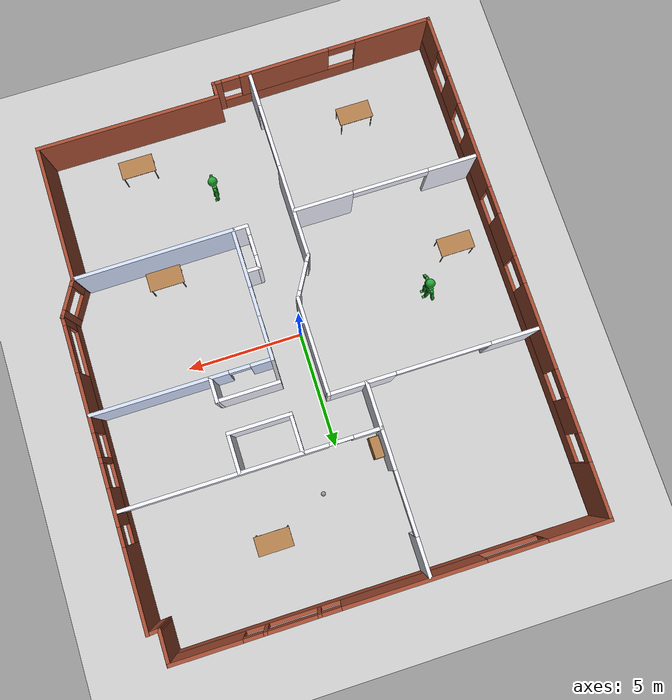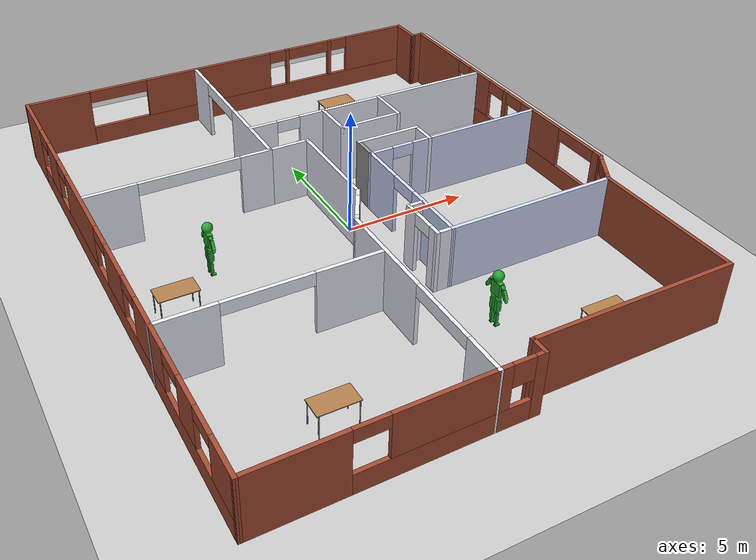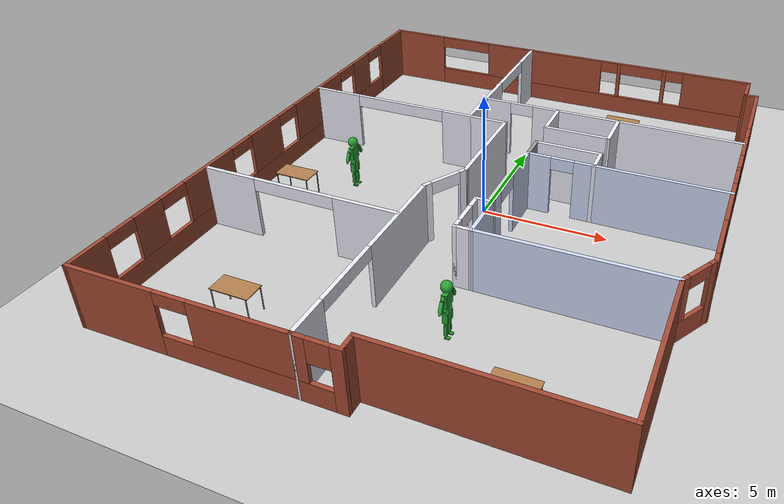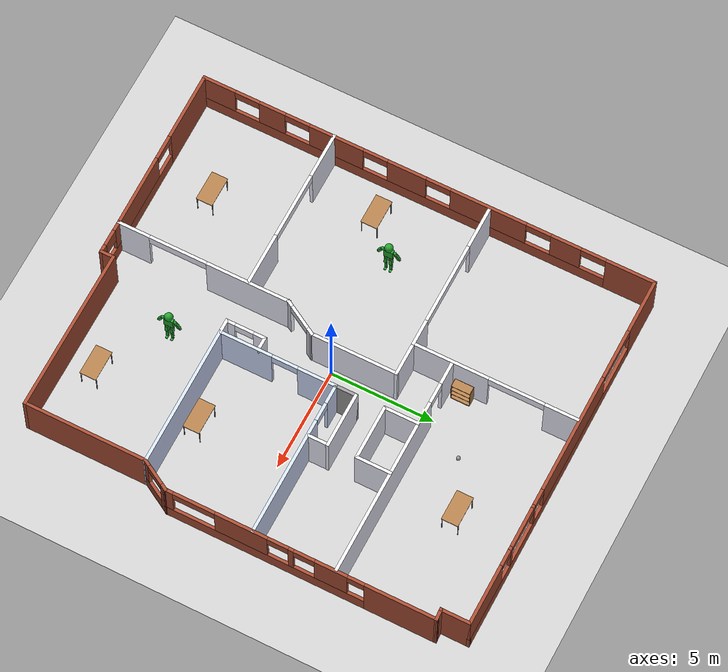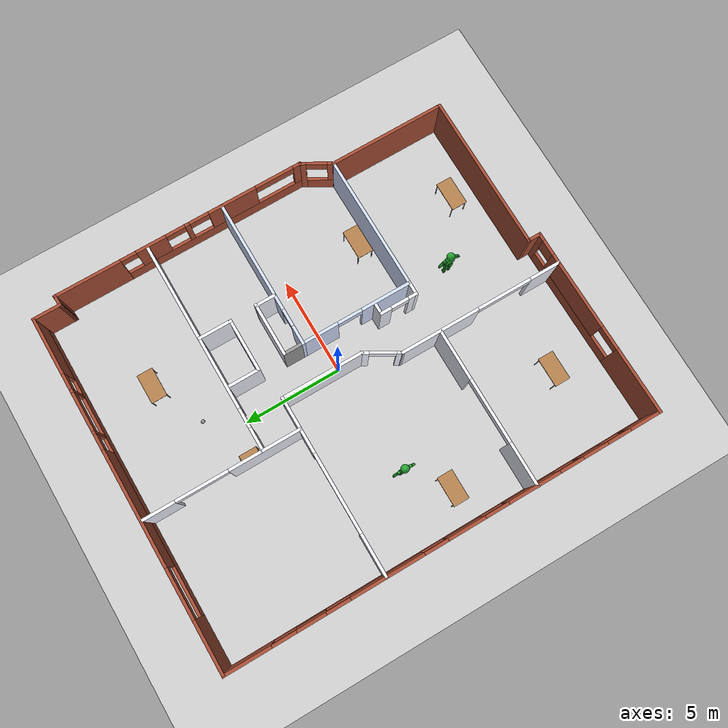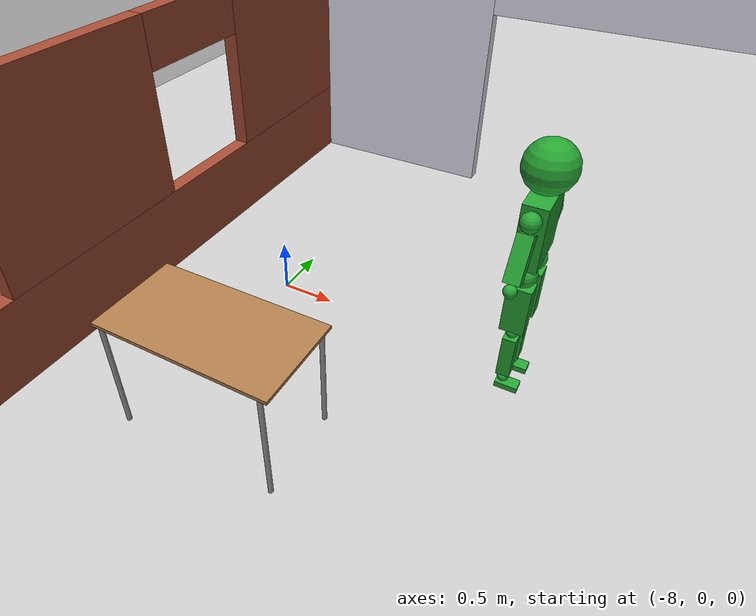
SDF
<sdf version="1.7">
 <world name="default">
  <light name="sun" type="directional">
   <pose>0 0 10 0 -0 0</pose>
   <diffuse>0.8 0.8 0.8 1</diffuse>
   <specular>0.2 0.2 0.2 1</specular>
   <attenuation>
    <range>1000</range>
    <constant>0.9</constant>
    <linear>0.01</linear>
    <quadratic>0.001</quadratic>
   </attenuation>
   <direction>-0.5 0.1 -0.9</direction>
   <spot><inner_angle>0</inner_angle><outer_angle>0</outer_angle><falloff>0</falloff></spot>
  </light>
  <model name="ground_plane">
   <static>1</static>
   <link name="link">
    <collision name="collision">
     <geometry><plane><normal>0 0 1</normal><size>100 100</size></plane></geometry>
     <surface>
      <contact><collide_bitmask>65535</collide_bitmask></contact>
      <friction><ode><mu>100</mu><mu2>50</mu2></ode></friction>
     </surface>
    </collision>
    <visual name="visual">
     <cast_shadows>0</cast_shadows>
     <geometry><plane><normal>0 0 1</normal><size>100 100</size></plane></geometry>
     <material>
      <script><uri>file://media/materials/scripts/gazebo.material</uri><name>Gazebo/Grey</name></script>
     </material>
    </visual>
   </link>
  </model>
  <gravity>0 0 -9.8</gravity>
  <magnetic_field>6e-06 2.3e-05 -4.2e-05</magnetic_field>
  <atmosphere type="adiabatic"/>
  <physics type="ode">
   <max_step_size>0.001</max_step_size>
   <real_time_factor>1</real_time_factor>
   <real_time_update_rate>1000</real_time_update_rate>
  </physics>
  <scene><ambient>0.4 0.4 0.4 1</ambient><background>0.7 0.7 0.7 1</background><shadows>1</shadows></scene>
  <spherical_coordinates>
   <surface_model>EARTH_WGS84</surface_model>
   <latitude_deg>0</latitude_deg>
   <longitude_deg>0</longitude_deg>
   <elevation>0</elevation>
   <heading_deg>0</heading_deg>
  </spherical_coordinates>
  <model name="Apartment 1023">
   <pose>-0.101328 -0.086897 0 0 -0 0</pose>
   <link name="Wall_0">
    <pose>9.15391 3.30895 0 0 0 -1.5708</pose>
    <visual name="Wall_0_Visual_0">
     <pose>-4.77738 0 1.25 0 -0 0</pose>
     <geometry><box><size>3.44524 0.15 2.5</size></box></geometry>
     <material>
      <script><uri>file://media/materials/scripts/gazebo.material</uri><name>Gazebo/Bricks</name></script>
      <ambient>1 1 1 1</ambient>
     </material>
     <meta><layer>0</layer></meta>
    </visual>
    <collision name="Wall_0_Collision_0">
     <geometry><box><size>3.44524 0.15 2.5</size></box></geometry>
     <pose>-4.77738 0 1.25 0 -0 0</pose>
    </collision>
    <visual name="Wall_0_Visual_1">
     <pose>1.72262 0 0.4 0 -0 0</pose>
     <geometry><box><size>9.55476 0.15 0.8</size></box></geometry>
     <material>
      <script><uri>file://media/materials/scripts/gazebo.material</uri><name>Gazebo/Bricks</name></script>
      <ambient>1 1 1 1</ambient>
     </material>
     <meta><layer>0</layer></meta>
    </visual>
    <collision name="Wall_0_Collision_1">
     <geometry><box><size>9.55476 0.15 0.8</size></box></geometry>
     <pose>1.72262 0 0.4 0 -0 0</pose>
    </collision>
    <visual name="Wall_0_Visual_2">
     <pose>-1.48168 0 1.65 0 -0 0</pose>
     <geometry><box><size>1.54617 0.15 1.7</size></box></geometry>
     <material>
      <script><uri>file://media/materials/scripts/gazebo.material</uri><name>Gazebo/Bricks</name></script>
      <ambient>1 1 1 1</ambient>
     </material>
     <meta><layer>0</layer></meta>
    </visual>
    <collision name="Wall_0_Collision_2">
     <geometry><box><size>1.54617 0.15 1.7</size></box></geometry>
     <pose>-1.48168 0 1.65 0 -0 0</pose>
    </collision>
    <visual name="Wall_0_Visual_3">
     <pose>0.414924 0 1.65 0 -0 0</pose>
     <geometry><box><size>0.247041 0.15 1.7</size></box></geometry>
     <material>
      <script><uri>file://media/materials/scripts/gazebo.material</uri><name>Gazebo/Bricks</name></script>
      <ambient>1 1 1 1</ambient>
     </material>
     <meta><layer>0</layer></meta>
    </visual>
    <collision name="Wall_0_Collision_3">
     <geometry><box><size>0.247041 0.15 1.7</size></box></geometry>
     <pose>0.414924 0 1.65 0 -0 0</pose>
    </collision>
    <visual name="Wall_0_Visual_4">
     <pose>2.79392 0 1.65 0 -0 0</pose>
     <geometry><box><size>2.51094 0.15 1.7</size></box></geometry>
     <material>
      <script><uri>file://media/materials/scripts/gazebo.material</uri><name>Gazebo/Bricks</name></script>
      <ambient>1 1 1 1</ambient>
     </material>
     <meta><layer>0</layer></meta>
    </visual>
    <collision name="Wall_0_Collision_4">
     <geometry><box><size>2.51094 0.15 1.7</size></box></geometry>
     <pose>2.79392 0 1.65 0 -0 0</pose>
    </collision>
    <visual name="Wall_0_Visual_5">
     <pose>6.27469 0 1.65 0 -0 0</pose>
     <geometry><box><size>0.450614 0.15 1.7</size></box></geometry>
     <material>
      <script><uri>file://media/materials/scripts/gazebo.material</uri><name>Gazebo/Bricks</name></script>
      <ambient>1 1 1 1</ambient>
     </material>
     <meta><layer>0</layer></meta>
    </visual>
    <collision name="Wall_0_Collision_5">
     <geometry><box><size>0.450614 0.15 1.7</size></box></geometry>
     <pose>6.27469 0 1.65 0 -0 0</pose>
    </collision>
    <visual name="Wall_0_Visual_6">
     <pose>-2.65476 0 2.25 0 -0 0</pose>
     <geometry><box><size>0.8 0.15 0.5</size></box></geometry>
     <material>
      <script><uri>file://media/materials/scripts/gazebo.material</uri><name>Gazebo/Bricks</name></script>
      <ambient>1 1 1 1</ambient>
     </material>
     <meta><layer>0</layer></meta>
    </visual>
    <collision name="Wall_0_Collision_6">
     <geometry><box><size>0.8 0.15 0.5</size></box></geometry>
     <pose>-2.65476 0 2.25 0 -0 0</pose>
    </collision>
    <visual name="Wall_0_Visual_7">
     <pose>-0.208596 0 2.25 0 -0 0</pose>
     <geometry><box><size>1 0.15 0.5</size></box></geometry>
     <material>
      <script><uri>file://media/materials/scripts/gazebo.material</uri><name>Gazebo/Bricks</name></script>
      <ambient>1 1 1 1</ambient>
     </material>
     <meta><layer>0</layer></meta>
    </visual>
    <collision name="Wall_0_Collision_7">
     <geometry><box><size>1 0.15 0.5</size></box></geometry>
     <pose>-0.208596 0 2.25 0 -0 0</pose>
    </collision>
    <visual name="Wall_0_Visual_8">
     <pose>1.03845 0 2.25 0 -0 0</pose>
     <geometry><box><size>1 0.15 0.5</size></box></geometry>
     <material>
      <script><uri>file://media/materials/scripts/gazebo.material</uri><name>Gazebo/Bricks</name></script>
      <ambient>1 1 1 1</ambient>
     </material>
     <meta><layer>0</layer></meta>
    </visual>
    <collision name="Wall_0_Collision_8">
     <geometry><box><size>1 0.15 0.5</size></box></geometry>
     <pose>1.03845 0 2.25 0 -0 0</pose>
    </collision>
    <visual name="Wall_0_Visual_9">
     <pose>5.04939 0 2.25 0 -0 0</pose>
     <geometry><box><size>2 0.15 0.5</size></box></geometry>
     <material>
      <script><uri>file://media/materials/scripts/gazebo.material</uri><name>Gazebo/Bricks</name></script>
      <ambient>1 1 1 1</ambient>
     </material>
     <meta><layer>0</layer></meta>
    </visual>
    <collision name="Wall_0_Collision_9">
     <geometry><box><size>2 0.15 0.5</size></box></geometry>
     <pose>5.04939 0 2.25 0 -0 0</pose>
    </collision>
   </link>
   <link name="Wall_1">
    <pose>8.75391 -3.80888 0 0 0 -2.0944</pose>
    <visual name="Wall_1_Visual_0">
     <pose>-0.689205 0 1.25 0 -0 0</pose>
     <geometry><box><size>0.371589 0.15 2.5</size></box></geometry>
     <material>
      <script><uri>file://media/materials/scripts/gazebo.material</uri><name>Gazebo/Bricks</name></script>
      <ambient>1 1 1 1</ambient>
     </material>
     <meta><layer>0</layer></meta>
    </visual>
    <collision name="Wall_1_Collision_0">
     <geometry><box><size>0.371589 0.15 2.5</size></box></geometry>
     <pose>-0.689205 0 1.25 0 -0 0</pose>
    </collision>
    <visual name="Wall_1_Visual_1">
     <pose>0.185795 0 0.4 0 -0 0</pose>
     <geometry><box><size>1.37841 0.15 0.8</size></box></geometry>
     <material>
      <script><uri>file://media/materials/scripts/gazebo.material</uri><name>Gazebo/Bricks</name></script>
      <ambient>1 1 1 1</ambient>
     </material>
     <meta><layer>0</layer></meta>
    </visual>
    <collision name="Wall_1_Collision_1">
     <geometry><box><size>1.37841 0.15 0.8</size></box></geometry>
     <pose>0.185795 0 0.4 0 -0 0</pose>
    </collision>
    <visual name="Wall_1_Visual_2">
     <pose>0.685795 0 1.65 0 -0 0</pose>
     <geometry><box><size>0.378411 0.15 1.7</size></box></geometry>
     <material>
      <script><uri>file://media/materials/scripts/gazebo.material</uri><name>Gazebo/Bricks</name></script>
      <ambient>1 1 1 1</ambient>
     </material>
     <meta><layer>0</layer></meta>
    </visual>
    <collision name="Wall_1_Collision_2">
     <geometry><box><size>0.378411 0.15 1.7</size></box></geometry>
     <pose>0.685795 0 1.65 0 -0 0</pose>
    </collision>
    <visual name="Wall_1_Visual_3">
     <pose>-0.003411 0 2.25 0 -0 0</pose>
     <geometry><box><size>1 0.15 0.5</size></box></geometry>
     <material>
      <script><uri>file://media/materials/scripts/gazebo.material</uri><name>Gazebo/Bricks</name></script>
      <ambient>1 1 1 1</ambient>
     </material>
     <meta><layer>0</layer></meta>
    </visual>
    <collision name="Wall_1_Collision_3">
     <geometry><box><size>1 0.15 0.5</size></box></geometry>
     <pose>-0.003411 0 2.25 0 -0 0</pose>
    </collision>
   </link>
   <link name="Wall_10">
    <pose>-1.77108 7.02545 0 0 -0 1.5708</pose>
    <visual name="Wall_10_Visual_0">
     <pose>-2.14904 0 1.25 0 -0 0</pose>
     <geometry><box><size>3.70192 0.15 2.5</size></box></geometry>
     <material>
      <script><uri>file://media/materials/scripts/gazebo.material</uri><name>Gazebo/Grey</name></script>
      <ambient>0.941176 0.94902 1 1</ambient>
     </material>
     <meta><layer>0</layer></meta>
    </visual>
    <collision name="Wall_10_Collision_0">
     <geometry><box><size>3.70192 0.15 2.5</size></box></geometry>
     <pose>-2.14904 0 1.25 0 -0 0</pose>
    </collision>
    <visual name="Wall_10_Visual_1">
     <pose>3.18043 0 1.25 0 -0 0</pose>
     <geometry><box><size>1.63914 0.15 2.5</size></box></geometry>
     <material>
      <script><uri>file://media/materials/scripts/gazebo.material</uri><name>Gazebo/Grey</name></script>
      <ambient>0.941176 0.94902 1 1</ambient>
     </material>
     <meta><layer>0</layer></meta>
    </visual>
    <collision name="Wall_10_Collision_1">
     <geometry><box><size>1.63914 0.15 2.5</size></box></geometry>
     <pose>3.18043 0 1.25 0 -0 0</pose>
    </collision>
    <visual name="Wall_10_Visual_2">
     <pose>1.03139 0 2.25 0 -0 0</pose>
     <geometry><box><size>2.65894 0.15 0.5</size></box></geometry>
     <material>
      <script><uri>file://media/materials/scripts/gazebo.material</uri><name>Gazebo/Grey</name></script>
      <ambient>0.941176 0.94902 1 1</ambient>
     </material>
     <meta><layer>0</layer></meta>
    </visual>
    <collision name="Wall_10_Collision_2">
     <geometry><box><size>2.65894 0.15 0.5</size></box></geometry>
     <pose>1.03139 0 2.25 0 -0 0</pose>
    </collision>
   </link>
   <link name="Wall_13">
    <pose>-0.246085 11.0505 0 0 -0 0</pose>
    <visual name="Wall_13_Visual_0">
     <pose>-7.65813 0 1.25 0 -0 0</pose>
     <geometry><box><size>2.68375 0.15 2.5</size></box></geometry>
     <material>
      <script><uri>file://media/materials/scripts/gazebo.material</uri><name>Gazebo/Bricks</name></script>
      <ambient>1 1 1 1</ambient>
     </material>
     <meta><layer>0</layer></meta>
    </visual>
    <collision name="Wall_13_Collision_0">
     <geometry><box><size>2.68375 0.15 2.5</size></box></geometry>
     <pose>-7.65813 0 1.25 0 -0 0</pose>
    </collision>
    <visual name="Wall_13_Visual_1">
     <pose>1.34187 0 0.4 0 -0 0</pose>
     <geometry><box><size>15.3163 0.15 0.8</size></box></geometry>
     <material>
      <script><uri>file://media/materials/scripts/gazebo.material</uri><name>Gazebo/Bricks</name></script>
      <ambient>1 1 1 1</ambient>
     </material>
     <meta><layer>0</layer></meta>
    </visual>
    <collision name="Wall_13_Collision_1">
     <geometry><box><size>15.3163 0.15 0.8</size></box></geometry>
     <pose>1.34187 0 0.4 0 -0 0</pose>
    </collision>
    <visual name="Wall_13_Visual_2">
     <pose>-0.874893 0 1.65 0 -0 0</pose>
     <geometry><box><size>5.88271 0.15 1.7</size></box></geometry>
     <material>
      <script><uri>file://media/materials/scripts/gazebo.material</uri><name>Gazebo/Bricks</name></script>
      <ambient>1 1 1 1</ambient>
     </material>
     <meta><layer>0</layer></meta>
    </visual>
    <collision name="Wall_13_Collision_2">
     <geometry><box><size>5.88271 0.15 1.7</size></box></geometry>
     <pose>-0.874893 0 1.65 0 -0 0</pose>
    </collision>
    <visual name="Wall_13_Visual_3">
     <pose>2.94577 0 1.65 0 -0 0</pose>
     <geometry><box><size>0.15862 0.15 1.7</size></box></geometry>
     <material>
      <script><uri>file://media/materials/scripts/gazebo.material</uri><name>Gazebo/Bricks</name></script>
      <ambient>1 1 1 1</ambient>
     </material>
     <meta><layer>0</layer></meta>
    </visual>
    <collision name="Wall_13_Collision_3">
     <geometry><box><size>0.15862 0.15 1.7</size></box></geometry>
     <pose>2.94577 0 1.65 0 -0 0</pose>
    </collision>
    <visual name="Wall_13_Visual_4">
     <pose>5.10951 0 1.65 0 -0 0</pose>
     <geometry><box><size>0.168859 0.15 1.7</size></box></geometry>
     <material>
      <script><uri>file://media/materials/scripts/gazebo.material</uri><name>Gazebo/Bricks</name></script>
      <ambient>1 1 1 1</ambient>
     </material>
     <meta><layer>0</layer></meta>
    </visual>
    <collision name="Wall_13_Collision_4">
     <geometry><box><size>0.168859 0.15 1.7</size></box></geometry>
     <pose>5.10951 0 1.65 0 -0 0</pose>
    </collision>
    <visual name="Wall_13_Visual_5">
     <pose>7.49697 0 1.65 0 -0 0</pose>
     <geometry><box><size>3.00606 0.15 1.7</size></box></geometry>
     <material>
      <script><uri>file://media/materials/scripts/gazebo.material</uri><name>Gazebo/Bricks</name></script>
      <ambient>1 1 1 1</ambient>
     </material>
     <meta><layer>0</layer></meta>
    </visual>
    <collision name="Wall_13_Collision_5">
     <geometry><box><size>3.00606 0.15 1.7</size></box></geometry>
     <pose>7.49697 0 1.65 0 -0 0</pose>
    </collision>
    <visual name="Wall_13_Visual_6">
     <pose>-5.06625 0 2.25 0 -0 0</pose>
     <geometry><box><size>2.5 0.15 0.5</size></box></geometry>
     <material>
      <script><uri>file://media/materials/scripts/gazebo.material</uri><name>Gazebo/Bricks</name></script>
      <ambient>1 1 1 1</ambient>
     </material>
     <meta><layer>0</layer></meta>
    </visual>
    <collision name="Wall_13_Collision_6">
     <geometry><box><size>2.5 0.15 0.5</size></box></geometry>
     <pose>-5.06625 0 2.25 0 -0 0</pose>
    </collision>
    <visual name="Wall_13_Visual_7">
     <pose>2.46646 0 2.25 0 -0 0</pose>
     <geometry><box><size>0.8 0.15 0.5</size></box></geometry>
     <material>
      <script><uri>file://media/materials/scripts/gazebo.material</uri><name>Gazebo/Bricks</name></script>
      <ambient>1 1 1 1</ambient>
     </material>
     <meta><layer>0</layer></meta>
    </visual>
    <collision name="Wall_13_Collision_7">
     <geometry><box><size>0.8 0.15 0.5</size></box></geometry>
     <pose>2.46646 0 2.25 0 -0 0</pose>
    </collision>
    <visual name="Wall_13_Visual_8">
     <pose>4.02508 0 2.25 0 -0 0</pose>
     <geometry><box><size>2 0.15 0.5</size></box></geometry>
     <material>
      <script><uri>file://media/materials/scripts/gazebo.material</uri><name>Gazebo/Bricks</name></script>
      <ambient>1 1 1 1</ambient>
     </material>
     <meta><layer>0</layer></meta>
    </visual>
    <collision name="Wall_13_Collision_8">
     <geometry><box><size>2 0.15 0.5</size></box></geometry>
     <pose>4.02508 0 2.25 0 -0 0</pose>
    </collision>
    <visual name="Wall_13_Visual_9">
     <pose>5.59394 0 2.25 0 -0 0</pose>
     <geometry><box><size>0.8 0.15 0.5</size></box></geometry>
     <material>
      <script><uri>file://media/materials/scripts/gazebo.material</uri><name>Gazebo/Bricks</name></script>
      <ambient>1 1 1 1</ambient>
     </material>
     <meta><layer>0</layer></meta>
    </visual>
    <collision name="Wall_13_Collision_9">
     <geometry><box><size>0.8 0.15 0.5</size></box></geometry>
     <pose>5.59394 0 2.25 0 -0 0</pose>
    </collision>
   </link>
   <link name="Wall_14">
    <collision name="Wall_14_Collision">
     <geometry><box><size>1.5 0.15 2.5</size></box></geometry>
     <pose>0 0 1.25 0 -0 0</pose>
    </collision>
    <visual name="Wall_14_Visual">
     <pose>0 0 1.25 0 -0 0</pose>
     <geometry><box><size>1.5 0.15 2.5</size></box></geometry>
     <material>
      <script><uri>file://media/materials/scripts/gazebo.material</uri><name>Gazebo/Bricks</name></script>
      <ambient>1 1 1 1</ambient>
     </material>
     <meta><layer>0</layer></meta>
    </visual>
    <pose>8.67891 10.3755 0 0 0 -1.5708</pose>
   </link>
   <link name="Wall_15">
    <collision name="Wall_15_Collision">
     <geometry><box><size>0.626179 0.15 2.5</size></box></geometry>
     <pose>0 0 1.25 0 -0 0</pose>
    </collision>
    <visual name="Wall_15_Visual">
     <pose>0 0 1.25 0 -0 0</pose>
     <geometry><box><size>0.626179 0.15 2.5</size></box></geometry>
     <material>
      <script><uri>file://media/materials/scripts/gazebo.material</uri><name>Gazebo/Bricks</name></script>
      <ambient>1 1 1 1</ambient>
     </material>
     <meta><layer>0</layer></meta>
    </visual>
    <pose>8.91642 9.7172 0 0 -0 0.070396</pose>
   </link>
   <link name="Wall_17">
    <pose>3.65986 4.99702 0 0 -0 0</pose>
    <visual name="Wall_17_Visual_0">
     <pose>-4.88064 0 1.25 0 -0 0</pose>
     <geometry><box><size>1.23872 0.15 2.5</size></box></geometry>
     <material>
      <script><uri>file://media/materials/scripts/gazebo.material</uri><name>Gazebo/Grey</name></script>
      <ambient>0.941176 0.94902 1 1</ambient>
     </material>
     <meta><layer>0</layer></meta>
    </visual>
    <collision name="Wall_17_Collision_0">
     <geometry><box><size>1.23872 0.15 2.5</size></box></geometry>
     <pose>-4.88064 0 1.25 0 -0 0</pose>
    </collision>
    <visual name="Wall_17_Visual_1">
     <pose>1.11936 0 1.25 0 -0 0</pose>
     <geometry><box><size>8.76128 0.15 2.5</size></box></geometry>
     <material>
      <script><uri>file://media/materials/scripts/gazebo.material</uri><name>Gazebo/Grey</name></script>
      <ambient>0.941176 0.94902 1 1</ambient>
     </material>
     <meta><layer>0</layer></meta>
    </visual>
    <collision name="Wall_17_Collision_1">
     <geometry><box><size>8.76128 0.15 2.5</size></box></geometry>
     <pose>1.11936 0 1.25 0 -0 0</pose>
    </collision>
    <visual name="Wall_17_Visual_2">
     <pose>-3.76128 0 2.25 0 -0 0</pose>
     <geometry><box><size>1 0.15 0.5</size></box></geometry>
     <material>
      <script><uri>file://media/materials/scripts/gazebo.material</uri><name>Gazebo/Grey</name></script>
      <ambient>0.941176 0.94902 1 1</ambient>
     </material>
     <meta><layer>0</layer></meta>
    </visual>
    <collision name="Wall_17_Collision_2">
     <geometry><box><size>1 0.15 0.5</size></box></geometry>
     <pose>-3.76128 0 2.25 0 -0 0</pose>
    </collision>
   </link>
   <link name="Wall_19">
    <collision name="Wall_19_Collision">
     <geometry><box><size>1.75 0.15 2.5</size></box></geometry>
     <pose>0 0 1.25 0 -0 0</pose>
    </collision>
    <visual name="Wall_19_Visual">
     <pose>0 0 1.25 0 -0 0</pose>
     <geometry><box><size>1.75 0.15 2.5</size></box></geometry>
     <material>
      <script><uri>file://media/materials/scripts/gazebo.material</uri><name>Gazebo/Grey</name></script>
      <ambient>0.941176 0.94902 1 1</ambient>
     </material>
     <meta><layer>0</layer></meta>
    </visual>
    <pose>1.50144 4.18379 0 0 0 -1.5708</pose>
   </link>
   <link name="Wall_2">
    <collision name="Wall_2_Collision">
     <geometry><box><size>6 0.15 2.5</size></box></geometry>
     <pose>0 0 1.25 0 -0 0</pose>
    </collision>
    <visual name="Wall_2_Visual">
     <pose>0 0 1.25 0 -0 0</pose>
     <geometry><box><size>6 0.15 2.5</size></box></geometry>
     <material>
      <script><uri>file://media/materials/scripts/gazebo.material</uri><name>Gazebo/Bricks</name></script>
      <ambient>1 1 1 1</ambient>
     </material>
     <meta><layer>0</layer></meta>
    </visual>
    <pose>8.35392 -7.4267 0 0 0 -1.5708</pose>
   </link>
   <link name="Wall_20">
    <collision name="Wall_20_Collision">
     <geometry><box><size>2.75 0.15 2.5</size></box></geometry>
     <pose>0 0 1.25 0 -0 0</pose>
    </collision>
    <visual name="Wall_20_Visual">
     <pose>0 0 1.25 0 -0 0</pose>
     <geometry><box><size>2.75 0.15 2.5</size></box></geometry>
     <material>
      <script><uri>file://media/materials/scripts/gazebo.material</uri><name>Gazebo/Grey</name></script>
      <ambient>0.941176 0.94902 1 1</ambient>
     </material>
     <meta><layer>0</layer></meta>
    </visual>
    <pose>2.80144 3.38379 0 0 -0 0</pose>
   </link>
   <link name="Wall_21">
    <collision name="Wall_21_Collision">
     <geometry><box><size>1.75 0.15 2.5</size></box></geometry>
     <pose>0 0 1.25 0 -0 0</pose>
    </collision>
    <visual name="Wall_21_Visual">
     <pose>0 0 1.25 0 -0 0</pose>
     <geometry><box><size>1.75 0.15 2.5</size></box></geometry>
     <material>
      <script><uri>file://media/materials/scripts/gazebo.material</uri><name>Gazebo/Grey</name></script>
      <ambient>0.941176 0.94902 1 1</ambient>
     </material>
     <meta><layer>0</layer></meta>
    </visual>
    <pose>4.10144 4.18379 0 0 -0 1.5708</pose>
   </link>
   <link name="Wall_3">
    <collision name="Wall_3_Collision">
     <geometry><box><size>8 0.15 2.5</size></box></geometry>
     <pose>0 0 1.25 0 -0 0</pose>
    </collision>
    <visual name="Wall_3_Visual">
     <pose>0 0 1.25 0 -0 0</pose>
     <geometry><box><size>8 0.15 2.5</size></box></geometry>
     <material>
      <script><uri>file://media/materials/scripts/gazebo.material</uri><name>Gazebo/Bricks</name></script>
      <ambient>1 1 1 1</ambient>
     </material>
     <meta><layer>0</layer></meta>
    </visual>
    <pose>4.42891 -10.3517 0 0 -0 3.14159</pose>
   </link>
   <link name="Wall_35">
    <pose>5.34861 1.06112 0 0 -0 3.14159</pose>
    <visual name="Wall_35_Visual_0">
     <pose>-0.950171 0 1.25 0 -0 0</pose>
     <geometry><box><size>5.84966 0.15 2.5</size></box></geometry>
     <material>
      <script><uri>file://media/materials/scripts/gazebo.material</uri><name>Gazebo/Grey</name></script>
      <ambient>0.827451 0.87451 1 1</ambient>
     </material>
     <meta><layer>0</layer></meta>
    </visual>
    <collision name="Wall_35_Collision_0">
     <geometry><box><size>5.84966 0.15 2.5</size></box></geometry>
     <pose>-0.950171 0 1.25 0 -0 0</pose>
    </collision>
    <visual name="Wall_35_Visual_1">
     <pose>3.37483 0 1.25 0 -0 0</pose>
     <geometry><box><size>1.00034 0.15 2.5</size></box></geometry>
     <material>
      <script><uri>file://media/materials/scripts/gazebo.material</uri><name>Gazebo/Grey</name></script>
      <ambient>0.827451 0.87451 1 1</ambient>
     </material>
     <meta><layer>0</layer></meta>
    </visual>
    <collision name="Wall_35_Collision_1">
     <geometry><box><size>1.00034 0.15 2.5</size></box></geometry>
     <pose>3.37483 0 1.25 0 -0 0</pose>
    </collision>
    <visual name="Wall_35_Visual_2">
     <pose>2.42466 0 2.25 0 -0 0</pose>
     <geometry><box><size>0.9 0.15 0.5</size></box></geometry>
     <material>
      <script><uri>file://media/materials/scripts/gazebo.material</uri><name>Gazebo/Grey</name></script>
      <ambient>0.827451 0.87451 1 1</ambient>
     </material>
     <meta><layer>0</layer></meta>
    </visual>
    <collision name="Wall_35_Collision_2">
     <geometry><box><size>0.9 0.15 0.5</size></box></geometry>
     <pose>2.42466 0 2.25 0 -0 0</pose>
    </collision>
   </link>
   <link name="Wall_36">
    <collision name="Wall_36_Collision">
     <geometry><box><size>1.12 0.15 2.5</size></box></geometry>
     <pose>0 0 1.25 0 -0 0</pose>
    </collision>
    <visual name="Wall_36_Visual">
     <pose>0 0 1.25 0 -0 0</pose>
     <geometry><box><size>1.12 0.15 2.5</size></box></geometry>
     <material>
      <script><uri>file://media/materials/scripts/gazebo.material</uri><name>Gazebo/Grey</name></script>
      <ambient>1 1 1 1</ambient>
     </material>
     <meta><layer>0</layer></meta>
    </visual>
    <pose>1.54861 1.54612 0 0 -0 1.5708</pose>
   </link>
   <link name="Wall_37">
    <collision name="Wall_37_Collision">
     <geometry><box><size>2.75 0.15 2.5</size></box></geometry>
     <pose>0 0 1.25 0 -0 0</pose>
    </collision>
    <visual name="Wall_37_Visual">
     <pose>0 0 1.25 0 -0 0</pose>
     <geometry><box><size>2.75 0.15 2.5</size></box></geometry>
     <material>
      <script><uri>file://media/materials/scripts/gazebo.material</uri><name>Gazebo/Grey</name></script>
      <ambient>0.941176 0.94902 1 1</ambient>
     </material>
     <meta><layer>0</layer></meta>
    </visual>
    <pose>2.85861 2.03112 0 0 -0 0</pose>
   </link>
   <link name="Wall_38">
    <collision name="Wall_38_Collision">
     <geometry><box><size>1.12 0.15 2.5</size></box></geometry>
     <pose>0 0 1.25 0 -0 0</pose>
    </collision>
    <visual name="Wall_38_Visual">
     <pose>0 0 1.25 0 -0 0</pose>
     <geometry><box><size>1.12 0.15 2.5</size></box></geometry>
     <material>
      <script><uri>file://media/materials/scripts/gazebo.material</uri><name>Gazebo/Grey</name></script>
      <ambient>0.941176 0.94902 1 1</ambient>
     </material>
     <meta><layer>0</layer></meta>
    </visual>
    <pose>4.14861 1.54612 0 0 0 -1.5708</pose>
   </link>
   <link name="Wall_4">
    <collision name="Wall_4_Collision">
     <geometry><box><size>0.75 0.15 2.5</size></box></geometry>
     <pose>0 0 1.25 0 -0 0</pose>
    </collision>
    <visual name="Wall_4_Visual">
     <pose>0 0 1.25 0 -0 0</pose>
     <geometry><box><size>0.75 0.15 2.5</size></box></geometry>
     <material>
      <script><uri>file://media/materials/scripts/gazebo.material</uri><name>Gazebo/Bricks</name></script>
      <ambient>1 1 1 1</ambient>
     </material>
     <meta><layer>0</layer></meta>
    </visual>
    <pose>0.503915 -10.6517 0 0 0 -1.5708</pose>
   </link>
   <link name="Wall_40">
    <pose>1.54861 -1.73888 0 0 0 -1.5708</pose>
    <visual name="Wall_40_Visual_0">
     <pose>-1.92511 0 1.25 0 -0 0</pose>
     <geometry><box><size>1.89977 0.15 2.5</size></box></geometry>
     <material>
      <script><uri>file://media/materials/scripts/gazebo.material</uri><name>Gazebo/Grey</name></script>
      <ambient>0.827451 0.87451 1 1</ambient>
     </material>
     <meta><layer>0</layer></meta>
    </visual>
    <collision name="Wall_40_Collision_0">
     <geometry><box><size>1.89977 0.15 2.5</size></box></geometry>
     <pose>-1.92511 0 1.25 0 -0 0</pose>
    </collision>
    <visual name="Wall_40_Visual_1">
     <pose>1.57489 0 1.25 0 -0 0</pose>
     <geometry><box><size>2.60023 0.15 2.5</size></box></geometry>
     <material>
      <script><uri>file://media/materials/scripts/gazebo.material</uri><name>Gazebo/Grey</name></script>
      <ambient>0.827451 0.87451 1 1</ambient>
     </material>
     <meta><layer>0</layer></meta>
    </visual>
    <collision name="Wall_40_Collision_1">
     <geometry><box><size>2.60023 0.15 2.5</size></box></geometry>
     <pose>1.57489 0 1.25 0 -0 0</pose>
    </collision>
    <visual name="Wall_40_Visual_2">
     <pose>-0.350228 0 2.25 0 -0 0</pose>
     <geometry><box><size>1.25 0.15 0.5</size></box></geometry>
     <material>
      <script><uri>file://media/materials/scripts/gazebo.material</uri><name>Gazebo/Grey</name></script>
      <ambient>0.827451 0.87451 1 1</ambient>
     </material>
     <meta><layer>0</layer></meta>
    </visual>
    <collision name="Wall_40_Collision_2">
     <geometry><box><size>1.25 0.15 0.5</size></box></geometry>
     <pose>-0.350228 0 2.25 0 -0 0</pose>
    </collision>
   </link>
   <link name="Wall_41">
    <collision name="Wall_41_Collision">
     <geometry><box><size>6.9554 0.15 2.5</size></box></geometry>
     <pose>0 0 1.25 0 -0 0</pose>
    </collision>
    <visual name="Wall_41_Visual">
     <pose>0 0 1.25 0 -0 0</pose>
     <geometry><box><size>6.9554 0.15 2.5</size></box></geometry>
     <material>
      <script><uri>file://media/materials/scripts/gazebo.material</uri><name>Gazebo/Grey</name></script>
      <ambient>0.827451 0.87451 1 1</ambient>
     </material>
     <meta><layer>0</layer></meta>
    </visual>
    <pose>4.95126 -4.52029 0 0 -0 0.005464</pose>
   </link>
   <link name="Wall_43">
    <collision name="Wall_43_Collision">
     <geometry><box><size>0.75 0.15 2.5</size></box></geometry>
     <pose>0 0 1.25 0 -0 0</pose>
    </collision>
    <visual name="Wall_43_Visual">
     <pose>0 0 1.25 0 -0 0</pose>
     <geometry><box><size>0.75 0.15 2.5</size></box></geometry>
     <material>
      <script><uri>file://media/materials/scripts/gazebo.material</uri><name>Gazebo/Grey</name></script>
      <ambient>0.941176 0.94902 1 1</ambient>
     </material>
     <meta><layer>0</layer></meta>
    </visual>
    <pose>1.24861 -4.53888 0 0 -0 3.14159</pose>
   </link>
   <link name="Wall_44">
    <pose>0.948612 -3.61388 0 0 -0 1.5708</pose>
    <visual name="Wall_44_Visual_0">
     <pose>-0.755696 0 1.25 0 -0 0</pose>
     <geometry><box><size>0.488608 0.15 2.5</size></box></geometry>
     <material>
      <script><uri>file://media/materials/scripts/gazebo.material</uri><name>Gazebo/Grey</name></script>
      <ambient>0.941176 0.94902 1 1</ambient>
     </material>
     <meta><layer>0</layer></meta>
    </visual>
    <collision name="Wall_44_Collision_0">
     <geometry><box><size>0.488608 0.15 2.5</size></box></geometry>
     <pose>-0.755696 0 1.25 0 -0 0</pose>
    </collision>
    <visual name="Wall_44_Visual_1">
     <pose>0.694304 0 1.25 0 -0 0</pose>
     <geometry><box><size>0.611392 0.15 2.5</size></box></geometry>
     <material>
      <script><uri>file://media/materials/scripts/gazebo.material</uri><name>Gazebo/Grey</name></script>
      <ambient>0.941176 0.94902 1 1</ambient>
     </material>
     <meta><layer>0</layer></meta>
    </visual>
    <collision name="Wall_44_Collision_1">
     <geometry><box><size>0.611392 0.15 2.5</size></box></geometry>
     <pose>0.694304 0 1.25 0 -0 0</pose>
    </collision>
    <visual name="Wall_44_Visual_2">
     <pose>-0.061392 0 2.25 0 -0 0</pose>
     <geometry><box><size>0.9 0.15 0.5</size></box></geometry>
     <material>
      <script><uri>file://media/materials/scripts/gazebo.material</uri><name>Gazebo/Grey</name></script>
      <ambient>0.941176 0.94902 1 1</ambient>
     </material>
     <meta><layer>0</layer></meta>
    </visual>
    <collision name="Wall_44_Collision_2">
     <geometry><box><size>0.9 0.15 0.5</size></box></geometry>
     <pose>-0.061392 0 2.25 0 -0 0</pose>
    </collision>
   </link>
   <link name="Wall_45">
    <collision name="Wall_45_Collision">
     <geometry><box><size>0.75 0.15 2.5</size></box></geometry>
     <pose>0 0 1.25 0 -0 0</pose>
    </collision>
    <visual name="Wall_45_Visual">
     <pose>0 0 1.25 0 -0 0</pose>
     <geometry><box><size>0.75 0.15 2.5</size></box></geometry>
     <material>
      <script><uri>file://media/materials/scripts/gazebo.material</uri><name>Gazebo/Grey</name></script>
      <ambient>0.941176 0.94902 1 1</ambient>
     </material>
     <meta><layer>0</layer></meta>
    </visual>
    <pose>1.24861 -2.68888 0 0 -0 0</pose>
   </link>
   <link name="Wall_47">
    <pose>-9.17108 0.000451 0 0 0 -1.5708</pose>
    <visual name="Wall_47_Visual_0">
     <pose>-9.92405 0 1.25 0 -0 0</pose>
     <geometry><box><size>2.4019 0.15 2.5</size></box></geometry>
     <material>
      <script><uri>file://media/materials/scripts/gazebo.material</uri><name>Gazebo/Bricks</name></script>
      <ambient>1 1 1 1</ambient>
     </material>
     <meta><layer>0</layer></meta>
    </visual>
    <collision name="Wall_47_Collision_0">
     <geometry><box><size>2.4019 0.15 2.5</size></box></geometry>
     <pose>-9.92405 0 1.25 0 -0 0</pose>
    </collision>
    <visual name="Wall_47_Visual_1">
     <pose>1.20095 0 0.4 0 -0 0</pose>
     <geometry><box><size>19.8481 0.15 0.8</size></box></geometry>
     <material>
      <script><uri>file://media/materials/scripts/gazebo.material</uri><name>Gazebo/Bricks</name></script>
      <ambient>1 1 1 1</ambient>
     </material>
     <meta><layer>0</layer></meta>
    </visual>
    <collision name="Wall_47_Collision_1">
     <geometry><box><size>19.8481 0.15 0.8</size></box></geometry>
     <pose>1.20095 0 0.4 0 -0 0</pose>
    </collision>
    <visual name="Wall_47_Visual_2">
     <pose>-6.79693 0 1.65 0 -0 0</pose>
     <geometry><box><size>1.45234 0.15 1.7</size></box></geometry>
     <material>
      <script><uri>file://media/materials/scripts/gazebo.material</uri><name>Gazebo/Bricks</name></script>
      <ambient>1 1 1 1</ambient>
     </material>
     <meta><layer>0</layer></meta>
    </visual>
    <collision name="Wall_47_Collision_2">
     <geometry><box><size>1.45234 0.15 1.7</size></box></geometry>
     <pose>-6.79693 0 1.65 0 -0 0</pose>
    </collision>
    <visual name="Wall_47_Visual_3">
     <pose>-3.02583 0 1.65 0 -0 0</pose>
     <geometry><box><size>3.68985 0.15 1.7</size></box></geometry>
     <material>
      <script><uri>file://media/materials/scripts/gazebo.material</uri><name>Gazebo/Bricks</name></script>
      <ambient>1 1 1 1</ambient>
     </material>
     <meta><layer>0</layer></meta>
    </visual>
    <collision name="Wall_47_Collision_3">
     <geometry><box><size>3.68985 0.15 1.7</size></box></geometry>
     <pose>-3.02583 0 1.65 0 -0 0</pose>
    </collision>
    <visual name="Wall_47_Visual_4">
     <pose>0.968038 0 1.65 0 -0 0</pose>
     <geometry><box><size>1.89789 0.15 1.7</size></box></geometry>
     <material>
      <script><uri>file://media/materials/scripts/gazebo.material</uri><name>Gazebo/Bricks</name></script>
      <ambient>1 1 1 1</ambient>
     </material>
     <meta><layer>0</layer></meta>
    </visual>
    <collision name="Wall_47_Collision_4">
     <geometry><box><size>1.89789 0.15 1.7</size></box></geometry>
     <pose>0.968038 0 1.65 0 -0 0</pose>
    </collision>
    <visual name="Wall_47_Visual_5">
     <pose>4.45073 0 1.65 0 -0 0</pose>
     <geometry><box><size>2.66751 0.15 1.7</size></box></geometry>
     <material>
      <script><uri>file://media/materials/scripts/gazebo.material</uri><name>Gazebo/Bricks</name></script>
      <ambient>1 1 1 1</ambient>
     </material>
     <meta><layer>0</layer></meta>
    </visual>
    <collision name="Wall_47_Collision_5">
     <geometry><box><size>2.66751 0.15 1.7</size></box></geometry>
     <pose>4.45073 0 1.65 0 -0 0</pose>
    </collision>
    <visual name="Wall_47_Visual_6">
     <pose>7.63333 0 1.65 0 -0 0</pose>
     <geometry><box><size>1.29769 0.15 1.7</size></box></geometry>
     <material>
      <script><uri>file://media/materials/scripts/gazebo.material</uri><name>Gazebo/Bricks</name></script>
      <ambient>1 1 1 1</ambient>
     </material>
     <meta><layer>0</layer></meta>
    </visual>
    <collision name="Wall_47_Collision_6">
     <geometry><box><size>1.29769 0.15 1.7</size></box></geometry>
     <pose>7.63333 0 1.65 0 -0 0</pose>
    </collision>
    <visual name="Wall_47_Visual_7">
     <pose>10.3036 0 1.65 0 -0 0</pose>
     <geometry><box><size>1.64282 0.15 1.7</size></box></geometry>
     <material>
      <script><uri>file://media/materials/scripts/gazebo.material</uri><name>Gazebo/Bricks</name></script>
      <ambient>1 1 1 1</ambient>
     </material>
     <meta><layer>0</layer></meta>
    </visual>
    <collision name="Wall_47_Collision_7">
     <geometry><box><size>1.64282 0.15 1.7</size></box></geometry>
     <pose>10.3036 0 1.65 0 -0 0</pose>
    </collision>
    <visual name="Wall_47_Visual_8">
     <pose>-8.1231 0 2.25 0 -0 0</pose>
     <geometry><box><size>1.2 0.15 0.5</size></box></geometry>
     <material>
      <script><uri>file://media/materials/scripts/gazebo.material</uri><name>Gazebo/Bricks</name></script>
      <ambient>1 1 1 1</ambient>
     </material>
     <meta><layer>0</layer></meta>
    </visual>
    <collision name="Wall_47_Collision_8">
     <geometry><box><size>1.2 0.15 0.5</size></box></geometry>
     <pose>-8.1231 0 2.25 0 -0 0</pose>
    </collision>
    <visual name="Wall_47_Visual_9">
     <pose>-5.47075 0 2.25 0 -0 0</pose>
     <geometry><box><size>1.2 0.15 0.5</size></box></geometry>
     <material>
      <script><uri>file://media/materials/scripts/gazebo.material</uri><name>Gazebo/Bricks</name></script>
      <ambient>1 1 1 1</ambient>
     </material>
     <meta><layer>0</layer></meta>
    </visual>
    <collision name="Wall_47_Collision_9">
     <geometry><box><size>1.2 0.15 0.5</size></box></geometry>
     <pose>-5.47075 0 2.25 0 -0 0</pose>
    </collision>
    <visual name="Wall_47_Visual_10">
     <pose>-0.580906 0 2.25 0 -0 0</pose>
     <geometry><box><size>1.2 0.15 0.5</size></box></geometry>
     <material>
      <script><uri>file://media/materials/scripts/gazebo.material</uri><name>Gazebo/Bricks</name></script>
      <ambient>1 1 1 1</ambient>
     </material>
     <meta><layer>0</layer></meta>
    </visual>
    <collision name="Wall_47_Collision_10">
     <geometry><box><size>1.2 0.15 0.5</size></box></geometry>
     <pose>-0.580906 0 2.25 0 -0 0</pose>
    </collision>
    <visual name="Wall_47_Visual_11">
     <pose>2.51698 0 2.25 0 -0 0</pose>
     <geometry><box><size>1.2 0.15 0.5</size></box></geometry>
     <material>
      <script><uri>file://media/materials/scripts/gazebo.material</uri><name>Gazebo/Bricks</name></script>
      <ambient>1 1 1 1</ambient>
     </material>
     <meta><layer>0</layer></meta>
    </visual>
    <collision name="Wall_47_Collision_11">
     <geometry><box><size>1.2 0.15 0.5</size></box></geometry>
     <pose>2.51698 0 2.25 0 -0 0</pose>
    </collision>
    <visual name="Wall_47_Visual_12">
     <pose>6.38449 0 2.25 0 -0 0</pose>
     <geometry><box><size>1.2 0.15 0.5</size></box></geometry>
     <material>
      <script><uri>file://media/materials/scripts/gazebo.material</uri><name>Gazebo/Bricks</name></script>
      <ambient>1 1 1 1</ambient>
     </material>
     <meta><layer>0</layer></meta>
    </visual>
    <collision name="Wall_47_Collision_12">
     <geometry><box><size>1.2 0.15 0.5</size></box></geometry>
     <pose>6.38449 0 2.25 0 -0 0</pose>
    </collision>
    <visual name="Wall_47_Visual_13">
     <pose>8.88218 0 2.25 0 -0 0</pose>
     <geometry><box><size>1.2 0.15 0.5</size></box></geometry>
     <material>
      <script><uri>file://media/materials/scripts/gazebo.material</uri><name>Gazebo/Bricks</name></script>
      <ambient>1 1 1 1</ambient>
     </material>
     <meta><layer>0</layer></meta>
    </visual>
    <collision name="Wall_47_Collision_13">
     <geometry><box><size>1.2 0.15 0.5</size></box></geometry>
     <pose>8.88218 0 2.25 0 -0 0</pose>
    </collision>
   </link>
   <link name="Wall_48">
    <pose>-5.13358 -11.0006 0 0 -0 0.012117</pose>
    <visual name="Wall_48_Visual_0">
     <pose>-2.40831 0 1.25 0 -0 0</pose>
     <geometry><box><size>3.40897 0.15 2.5</size></box></geometry>
     <material>
      <script><uri>file://media/materials/scripts/gazebo.material</uri><name>Gazebo/Bricks</name></script>
      <ambient>1 1 1 1</ambient>
     </material>
     <meta><layer>0</layer></meta>
    </visual>
    <collision name="Wall_48_Collision_0">
     <geometry><box><size>3.40897 0.15 2.5</size></box></geometry>
     <pose>-2.40831 0 1.25 0 -0 0</pose>
    </collision>
    <visual name="Wall_48_Visual_1">
     <pose>1.70449 0 0.4 0 -0 0</pose>
     <geometry><box><size>4.81662 0.15 0.8</size></box></geometry>
     <material>
      <script><uri>file://media/materials/scripts/gazebo.material</uri><name>Gazebo/Bricks</name></script>
      <ambient>1 1 1 1</ambient>
     </material>
     <meta><layer>0</layer></meta>
    </visual>
    <collision name="Wall_48_Collision_1">
     <geometry><box><size>4.81662 0.15 0.8</size></box></geometry>
     <pose>1.70449 0 0.4 0 -0 0</pose>
    </collision>
    <visual name="Wall_48_Visual_2">
     <pose>2.30449 0 1.65 0 -0 0</pose>
     <geometry><box><size>3.61662 0.15 1.7</size></box></geometry>
     <material>
      <script><uri>file://media/materials/scripts/gazebo.material</uri><name>Gazebo/Bricks</name></script>
      <ambient>1 1 1 1</ambient>
     </material>
     <meta><layer>0</layer></meta>
    </visual>
    <collision name="Wall_48_Collision_2">
     <geometry><box><size>3.61662 0.15 1.7</size></box></geometry>
     <pose>2.30449 0 1.65 0 -0 0</pose>
    </collision>
    <visual name="Wall_48_Visual_3">
     <pose>-0.103827 0 2.25 0 -0 0</pose>
     <geometry><box><size>1.2 0.15 0.5</size></box></geometry>
     <material>
      <script><uri>file://media/materials/scripts/gazebo.material</uri><name>Gazebo/Bricks</name></script>
      <ambient>1 1 1 1</ambient>
     </material>
     <meta><layer>0</layer></meta>
    </visual>
    <collision name="Wall_48_Collision_3">
     <geometry><box><size>1.2 0.15 0.5</size></box></geometry>
     <pose>-0.103827 0 2.25 0 -0 0</pose>
    </collision>
   </link>
   <link name="Wall_5">
    <pose>-0.296085 -10.9517 0 0 -0 3.14159</pose>
    <visual name="Wall_5_Visual_0">
     <pose>-0.664476 0 1.25 0 -0 0</pose>
     <geometry><box><size>0.421049 0.15 2.5</size></box></geometry>
     <material>
      <script><uri>file://media/materials/scripts/gazebo.material</uri><name>Gazebo/Bricks</name></script>
      <ambient>1 1 1 1</ambient>
     </material>
     <meta><layer>0</layer></meta>
    </visual>
    <collision name="Wall_5_Collision_0">
     <geometry><box><size>0.421049 0.15 2.5</size></box></geometry>
     <pose>-0.664476 0 1.25 0 -0 0</pose>
    </collision>
    <visual name="Wall_5_Visual_1">
     <pose>0.210524 0 0.4 0 -0 0</pose>
     <geometry><box><size>1.32895 0.15 0.8</size></box></geometry>
     <material>
      <script><uri>file://media/materials/scripts/gazebo.material</uri><name>Gazebo/Bricks</name></script>
      <ambient>1 1 1 1</ambient>
     </material>
     <meta><layer>0</layer></meta>
    </visual>
    <collision name="Wall_5_Collision_1">
     <geometry><box><size>1.32895 0.15 0.8</size></box></geometry>
     <pose>0.210524 0 0.4 0 -0 0</pose>
    </collision>
    <visual name="Wall_5_Visual_2">
     <pose>0.610524 0 1.65 0 -0 0</pose>
     <geometry><box><size>0.528951 0.15 1.7</size></box></geometry>
     <material>
      <script><uri>file://media/materials/scripts/gazebo.material</uri><name>Gazebo/Bricks</name></script>
      <ambient>1 1 1 1</ambient>
     </material>
     <meta><layer>0</layer></meta>
    </visual>
    <collision name="Wall_5_Collision_2">
     <geometry><box><size>0.528951 0.15 1.7</size></box></geometry>
     <pose>0.610524 0 1.65 0 -0 0</pose>
    </collision>
    <visual name="Wall_5_Visual_3">
     <pose>-0.053951 0 2.05 0 -0 0</pose>
     <geometry><box><size>0.8 0.15 0.9</size></box></geometry>
     <material>
      <script><uri>file://media/materials/scripts/gazebo.material</uri><name>Gazebo/Bricks</name></script>
      <ambient>1 1 1 1</ambient>
     </material>
     <meta><layer>0</layer></meta>
    </visual>
    <collision name="Wall_5_Collision_3">
     <geometry><box><size>0.8 0.15 0.9</size></box></geometry>
     <pose>-0.053951 0 2.05 0 -0 0</pose>
    </collision>
   </link>
   <link name="Wall_50">
    <pose>-5.44608 3.10045 0 0 -0 3.14159</pose>
    <visual name="Wall_50_Visual_0">
     <pose>-3.09255 0 1.25 0 -0 0</pose>
     <geometry><box><size>1.31491 0.15 2.5</size></box></geometry>
     <material>
      <script><uri>file://media/materials/scripts/gazebo.material</uri><name>Gazebo/Grey</name></script>
      <ambient>0.941176 0.94902 1 1</ambient>
     </material>
     <meta><layer>0</layer></meta>
    </visual>
    <collision name="Wall_50_Collision_0">
     <geometry><box><size>1.31491 0.15 2.5</size></box></geometry>
     <pose>-3.09255 0 1.25 0 -0 0</pose>
    </collision>
    <visual name="Wall_50_Visual_1">
     <pose>2.67291 0 1.25 0 -0 0</pose>
     <geometry><box><size>2.15418 0.15 2.5</size></box></geometry>
     <material>
      <script><uri>file://media/materials/scripts/gazebo.material</uri><name>Gazebo/Grey</name></script>
      <ambient>0.941176 0.94902 1 1</ambient>
     </material>
     <meta><layer>0</layer></meta>
    </visual>
    <collision name="Wall_50_Collision_1">
     <geometry><box><size>2.15418 0.15 2.5</size></box></geometry>
     <pose>2.67291 0 1.25 0 -0 0</pose>
    </collision>
    <visual name="Wall_50_Visual_2">
     <pose>-0.419639 0 2.25 0 -0 0</pose>
     <geometry><box><size>4.03091 0.15 0.5</size></box></geometry>
     <material>
      <script><uri>file://media/materials/scripts/gazebo.material</uri><name>Gazebo/Grey</name></script>
      <ambient>0.941176 0.94902 1 1</ambient>
     </material>
     <meta><layer>0</layer></meta>
    </visual>
    <collision name="Wall_50_Collision_2">
     <geometry><box><size>4.03091 0.15 0.5</size></box></geometry>
     <pose>-0.419639 0 2.25 0 -0 0</pose>
    </collision>
   </link>
   <link name="Wall_52">
    <pose>-5.1653 -4.58304 0 0 -0 3.14159</pose>
    <visual name="Wall_52_Visual_0">
     <pose>-2.78849 0 1.25 0 -0 0</pose>
     <geometry><box><size>2.60516 0.15 2.5</size></box></geometry>
     <material>
      <script><uri>file://media/materials/scripts/gazebo.material</uri><name>Gazebo/Grey</name></script>
      <ambient>0.941176 0.94902 1 1</ambient>
     </material>
     <meta><layer>0</layer></meta>
    </visual>
    <collision name="Wall_52_Collision_0">
     <geometry><box><size>2.60516 0.15 2.5</size></box></geometry>
     <pose>-2.78849 0 1.25 0 -0 0</pose>
    </collision>
    <visual name="Wall_52_Visual_1">
     <pose>2.94866 0 1.25 0 -0 0</pose>
     <geometry><box><size>2.28482 0.15 2.5</size></box></geometry>
     <material>
      <script><uri>file://media/materials/scripts/gazebo.material</uri><name>Gazebo/Grey</name></script>
      <ambient>0.941176 0.94902 1 1</ambient>
     </material>
     <meta><layer>0</layer></meta>
    </visual>
    <collision name="Wall_52_Collision_1">
     <geometry><box><size>2.28482 0.15 2.5</size></box></geometry>
     <pose>2.94866 0 1.25 0 -0 0</pose>
    </collision>
    <visual name="Wall_52_Visual_2">
     <pose>0.160168 0 2.25 0 -0 0</pose>
     <geometry><box><size>3.29216 0.15 0.5</size></box></geometry>
     <material>
      <script><uri>file://media/materials/scripts/gazebo.material</uri><name>Gazebo/Grey</name></script>
      <ambient>0.941176 0.94902 1 1</ambient>
     </material>
     <meta><layer>0</layer></meta>
    </visual>
    <collision name="Wall_52_Collision_2">
     <geometry><box><size>3.29216 0.15 0.5</size></box></geometry>
     <pose>0.160168 0 2.25 0 -0 0</pose>
    </collision>
   </link>
   <link name="Wall_6">
    <pose>-1.09608 -6.7767 0 0 -0 1.5708</pose>
    <visual name="Wall_6_Visual_0">
     <pose>-3.44649 0 1.25 0 -0 0</pose>
     <geometry><box><size>1.60702 0.15 2.5</size></box></geometry>
     <material>
      <script><uri>file://media/materials/scripts/gazebo.material</uri><name>Gazebo/Grey</name></script>
      <ambient>0.941176 0.94902 1 1</ambient>
     </material>
     <meta><layer>0</layer></meta>
    </visual>
    <collision name="Wall_6_Collision_0">
     <geometry><box><size>1.60702 0.15 2.5</size></box></geometry>
     <pose>-3.44649 0 1.25 0 -0 0</pose>
    </collision>
    <visual name="Wall_6_Visual_1">
     <pose>2.20334 0 1.25 0 -0 0</pose>
     <geometry><box><size>4.09333 0.15 2.5</size></box></geometry>
     <material>
      <script><uri>file://media/materials/scripts/gazebo.material</uri><name>Gazebo/Grey</name></script>
      <ambient>0.941176 0.94902 1 1</ambient>
     </material>
     <meta><layer>0</layer></meta>
    </visual>
    <collision name="Wall_6_Collision_1">
     <geometry><box><size>4.09333 0.15 2.5</size></box></geometry>
     <pose>2.20334 0 1.25 0 -0 0</pose>
    </collision>
    <visual name="Wall_6_Visual_2">
     <pose>-1.24315 0 2.25 0 -0 0</pose>
     <geometry><box><size>2.79965 0.15 0.5</size></box></geometry>
     <material>
      <script><uri>file://media/materials/scripts/gazebo.material</uri><name>Gazebo/Grey</name></script>
      <ambient>0.941176 0.94902 1 1</ambient>
     </material>
     <meta><layer>0</layer></meta>
    </visual>
    <collision name="Wall_6_Collision_2">
     <geometry><box><size>2.79965 0.15 0.5</size></box></geometry>
     <pose>-1.24315 0 2.25 0 -0 0</pose>
    </collision>
   </link>
   <link name="Wall_7">
    <pose>-0.633584 -1.80062 0 0 -0 1.0472</pose>
    <visual name="Wall_7_Visual_0">
     <pose>-0.822223 0 1.25 0 -0 0</pose>
     <geometry><box><size>0.355553 0.15 2.5</size></box></geometry>
     <material>
      <script><uri>file://media/materials/scripts/gazebo.material</uri><name>Gazebo/Grey</name></script>
      <ambient>0.941176 0.94902 1 1</ambient>
     </material>
     <meta><layer>0</layer></meta>
    </visual>
    <collision name="Wall_7_Collision_0">
     <geometry><box><size>0.355553 0.15 2.5</size></box></geometry>
     <pose>-0.822223 0 1.25 0 -0 0</pose>
    </collision>
    <visual name="Wall_7_Visual_1">
     <pose>0.802777 0 1.25 0 -0 0</pose>
     <geometry><box><size>0.394447 0.15 2.5</size></box></geometry>
     <material>
      <script><uri>file://media/materials/scripts/gazebo.material</uri><name>Gazebo/Grey</name></script>
      <ambient>0.941176 0.94902 1 1</ambient>
     </material>
     <meta><layer>0</layer></meta>
    </visual>
    <collision name="Wall_7_Collision_1">
     <geometry><box><size>0.394447 0.15 2.5</size></box></geometry>
     <pose>0.802777 0 1.25 0 -0 0</pose>
    </collision>
    <visual name="Wall_7_Visual_2">
     <pose>-0.019447 0 2.25 0 -0 0</pose>
     <geometry><box><size>1.25 0.15 0.5</size></box></geometry>
     <material>
      <script><uri>file://media/materials/scripts/gazebo.material</uri><name>Gazebo/Grey</name></script>
      <ambient>0.941176 0.94902 1 1</ambient>
     </material>
     <meta><layer>0</layer></meta>
    </visual>
    <collision name="Wall_7_Collision_2">
     <geometry><box><size>1.25 0.15 0.5</size></box></geometry>
     <pose>-0.019447 0 2.25 0 -0 0</pose>
    </collision>
   </link>
   <link name="Wall_8">
    <collision name="Wall_8_Collision">
     <geometry><box><size>4.25 0.15 2.5</size></box></geometry>
     <pose>0 0 1.25 0 -0 0</pose>
    </collision>
    <visual name="Wall_8_Visual">
     <pose>0 0 1.25 0 -0 0</pose>
     <geometry><box><size>4.25 0.15 2.5</size></box></geometry>
     <material>
      <script><uri>file://media/materials/scripts/gazebo.material</uri><name>Gazebo/Grey</name></script>
      <ambient>0.941176 0.94902 1 1</ambient>
     </material>
     <meta><layer>0</layer></meta>
    </visual>
    <pose>-0.171085 1.05045 0 0 -0 1.5708</pose>
   </link>
   <link name="Wall_9">
    <collision name="Wall_9_Collision">
     <geometry><box><size>1.75 0.15 2.5</size></box></geometry>
     <pose>0 0 1.25 0 -0 0</pose>
    </collision>
    <visual name="Wall_9_Visual">
     <pose>0 0 1.25 0 -0 0</pose>
     <geometry><box><size>1.75 0.15 2.5</size></box></geometry>
     <material>
      <script><uri>file://media/materials/scripts/gazebo.material</uri><name>Gazebo/Grey</name></script>
      <ambient>0.941176 0.94902 1 1</ambient>
     </material>
     <meta><layer>0</layer></meta>
    </visual>
    <pose>-0.971085 3.10045 0 0 -0 3.14159</pose>
   </link>
   <static>1</static>
  </model>
  <model name="HumanoidRobot">
   <static>1</static>
   <link name="link_Foot_RT">
    <pose>0.98187 -0.173198 -0.379096 0 -0 0</pose>
    <inertial>
     <mass>1</mass>
     <inertia>
      <ixx>0.166667</ixx>
      <ixy>0</ixy>
      <ixz>0</ixz>
      <iyy>0.166667</iyy>
      <iyz>0</iyz>
      <izz>0.166667</izz>
     </inertia>
    </inertial>
    <visual name="visual">
     <geometry><box><size>0.19 0.11 0.05</size></box></geometry>
     <material>
      <lighting>1</lighting>
      <script><uri>file://media/materials/scripts/gazebo.material</uri><name>Gazebo/Green</name></script>
      <emissive>0 0 0 1</emissive>
      <shader type="vertex"><normal_map>__default__</normal_map></shader>
     </material>
    </visual>
    <collision name="collision">
     <geometry><box><size>0.19 0.11 0.05</size></box></geometry>
     <surface>
      <friction>
       <ode><mu>1</mu><mu2>1</mu2><fdir1>0 0 0</fdir1><slip1>0</slip1><slip2>0</slip2></ode>
       <torsional>
        <coefficient>1</coefficient>
        <patch_radius>0</patch_radius>
        <surface_radius>0</surface_radius>
        <use_patch_radius>1</use_patch_radius>
        <ode><slip>0</slip></ode>
       </torsional>
      </friction>
      <bounce><restitution_coefficient>0</restitution_coefficient><threshold>1e+06</threshold></bounce>
      <contact>
       <collide_without_contact>0</collide_without_contact>
       <collide_without_contact_bitmask>1</collide_without_contact_bitmask>
       <collide_bitmask>1</collide_bitmask>
       <ode>
        <soft_cfm>0</soft_cfm>
        <soft_erp>0.2</soft_erp>
        <kp>1e+13</kp>
        <kd>1</kd>
        <max_vel>0.01</max_vel>
        <min_depth>0</min_depth>
       </ode>
       <bullet>
        <split_impulse>1</split_impulse>
        <split_impulse_penetration_threshold>-0.01</split_impulse_penetration_threshold>
        <soft_cfm>0</soft_cfm>
        <soft_erp>0.2</soft_erp>
        <kp>1e+13</kp>
        <kd>1</kd>
       </bullet>
      </contact>
     </surface>
    </collision>
   </link>
   <link name="link_Ankle_RT">
    <pose>0.93687 -0.173198 -0.304096 0 -0 0</pose>
    <inertial>
     <mass>1</mass>
     <inertia><ixx>0.1</ixx><ixy>0</ixy><ixz>0</ixz><iyy>0.1</iyy><iyz>0</iyz><izz>0.1</izz></inertia>
    </inertial>
    <visual name="visual">
     <geometry><sphere><radius>0.05</radius></sphere></geometry>
     <material>
      <lighting>1</lighting>
      <script><uri>file://media/materials/scripts/gazebo.material</uri><name>Gazebo/Green</name></script>
      <emissive>0 0 0 1</emissive>
      <shader type="vertex"><normal_map>__default__</normal_map></shader>
     </material>
    </visual>
    <collision name="collision">
     <geometry><sphere><radius>0.05</radius></sphere></geometry>
     <surface>
      <friction>
       <ode><mu>1</mu><mu2>1</mu2><fdir1>0 0 0</fdir1><slip1>0</slip1><slip2>0</slip2></ode>
       <torsional>
        <coefficient>1</coefficient>
        <patch_radius>0</patch_radius>
        <surface_radius>0</surface_radius>
        <use_patch_radius>1</use_patch_radius>
        <ode><slip>0</slip></ode>
       </torsional>
      </friction>
      <bounce><restitution_coefficient>0</restitution_coefficient><threshold>1e+06</threshold></bounce>
      <contact>
       <collide_without_contact>0</collide_without_contact>
       <collide_without_contact_bitmask>1</collide_without_contact_bitmask>
       <collide_bitmask>1</collide_bitmask>
       <ode>
        <soft_cfm>0</soft_cfm>
        <soft_erp>0.2</soft_erp>
        <kp>1e+13</kp>
        <kd>1</kd>
        <max_vel>0.01</max_vel>
        <min_depth>0</min_depth>
       </ode>
       <bullet>
        <split_impulse>1</split_impulse>
        <split_impulse_penetration_threshold>-0.01</split_impulse_penetration_threshold>
        <soft_cfm>0</soft_cfm>
        <soft_erp>0.2</soft_erp>
        <kp>1e+13</kp>
        <kd>1</kd>
       </bullet>
      </contact>
     </surface>
    </collision>
   </link>
   <link name="link_Ankle_LT">
    <pose>0.939823 0.076802 -0.3041 0 -0 0</pose>
    <inertial>
     <mass>1</mass>
     <inertia><ixx>0.1</ixx><ixy>0</ixy><ixz>0</ixz><iyy>0.1</iyy><iyz>0</iyz><izz>0.1</izz></inertia>
    </inertial>
    <visual name="visual">
     <geometry><sphere><radius>0.05</radius></sphere></geometry>
     <material>
      <lighting>1</lighting>
      <script><uri>file://media/materials/scripts/gazebo.material</uri><name>Gazebo/Green</name></script>
      <emissive>0 0 0 1</emissive>
      <shader type="vertex"><normal_map>__default__</normal_map></shader>
     </material>
    </visual>
    <collision name="collision">
     <geometry><sphere><radius>0.05</radius></sphere></geometry>
     <surface>
      <friction>
       <ode><mu>1</mu><mu2>1</mu2><fdir1>0 0 0</fdir1><slip1>0</slip1><slip2>0</slip2></ode>
       <torsional>
        <coefficient>1</coefficient>
        <patch_radius>0</patch_radius>
        <surface_radius>0</surface_radius>
        <use_patch_radius>1</use_patch_radius>
        <ode><slip>0</slip></ode>
       </torsional>
      </friction>
      <bounce><restitution_coefficient>0</restitution_coefficient><threshold>1e+06</threshold></bounce>
      <contact>
       <collide_without_contact>0</collide_without_contact>
       <collide_without_contact_bitmask>1</collide_without_contact_bitmask>
       <collide_bitmask>1</collide_bitmask>
       <ode>
        <soft_cfm>0</soft_cfm>
        <soft_erp>0.2</soft_erp>
        <kp>1e+13</kp>
        <kd>1</kd>
        <max_vel>0.01</max_vel>
        <min_depth>0</min_depth>
       </ode>
       <bullet>
        <split_impulse>1</split_impulse>
        <split_impulse_penetration_threshold>-0.01</split_impulse_penetration_threshold>
        <soft_cfm>0</soft_cfm>
        <soft_erp>0.2</soft_erp>
        <kp>1e+13</kp>
        <kd>1</kd>
       </bullet>
      </contact>
     </surface>
    </collision>
   </link>
   <link name="link_Arm_RT">
    <pose>0.93687 -0.468195 1.0909 -0.5 0 0</pose>
    <inertial>
     <mass>1</mass>
     <inertia>
      <ixx>0.166667</ixx>
      <ixy>0</ixy>
      <ixz>0</ixz>
      <iyy>0.166667</iyy>
      <iyz>0</iyz>
      <izz>0.166667</izz>
     </inertia>
    </inertial>
    <visual name="visual">
     <geometry><box><size>0.12 0.12 0.35</size></box></geometry>
     <material>
      <lighting>1</lighting>
      <script><uri>file://media/materials/scripts/gazebo.material</uri><name>Gazebo/Green</name></script>
      <emissive>0 0 0 1</emissive>
      <shader type="vertex"><normal_map>__default__</normal_map></shader>
     </material>
    </visual>
    <collision name="collision">
     <geometry><box><size>0.12 0.12 0.35</size></box></geometry>
     <surface>
      <friction>
       <ode><mu>1</mu><mu2>1</mu2><fdir1>0 0 0</fdir1><slip1>0</slip1><slip2>0</slip2></ode>
       <torsional>
        <coefficient>1</coefficient>
        <patch_radius>0</patch_radius>
        <surface_radius>0</surface_radius>
        <use_patch_radius>1</use_patch_radius>
        <ode><slip>0</slip></ode>
       </torsional>
      </friction>
      <bounce><restitution_coefficient>0</restitution_coefficient><threshold>1e+06</threshold></bounce>
      <contact>
       <collide_without_contact>0</collide_without_contact>
       <collide_without_contact_bitmask>1</collide_without_contact_bitmask>
       <collide_bitmask>1</collide_bitmask>
       <ode>
        <soft_cfm>0</soft_cfm>
        <soft_erp>0.2</soft_erp>
        <kp>1e+13</kp>
        <kd>1</kd>
        <max_vel>0.01</max_vel>
        <min_depth>0</min_depth>
       </ode>
       <bullet>
        <split_impulse>1</split_impulse>
        <split_impulse_penetration_threshold>-0.01</split_impulse_penetration_threshold>
        <soft_cfm>0</soft_cfm>
        <soft_erp>0.2</soft_erp>
        <kp>1e+13</kp>
        <kd>1</kd>
       </bullet>
      </contact>
     </surface>
    </collision>
   </link>
   <link name="link_Arm_LT">
    <pose>0.939823 0.376802 1.0909 0.5 -0 0</pose>
    <inertial>
     <mass>1</mass>
     <inertia>
      <ixx>0.166667</ixx>
      <ixy>0</ixy>
      <ixz>0</ixz>
      <iyy>0.166667</iyy>
      <iyz>0</iyz>
      <izz>0.166667</izz>
     </inertia>
    </inertial>
    <visual name="visual">
     <geometry><box><size>0.12 0.12 0.35</size></box></geometry>
     <material>
      <lighting>1</lighting>
      <script><uri>file://media/materials/scripts/gazebo.material</uri><name>Gazebo/Green</name></script>
      <emissive>0 0 0 1</emissive>
      <shader type="vertex"><normal_map>__default__</normal_map></shader>
     </material>
    </visual>
    <collision name="collision">
     <geometry><box><size>0.12 0.12 0.35</size></box></geometry>
     <surface>
      <friction>
       <ode><mu>1</mu><mu2>1</mu2><fdir1>0 0 0</fdir1><slip1>0</slip1><slip2>0</slip2></ode>
       <torsional>
        <coefficient>1</coefficient>
        <patch_radius>0</patch_radius>
        <surface_radius>0</surface_radius>
        <use_patch_radius>1</use_patch_radius>
        <ode><slip>0</slip></ode>
       </torsional>
      </friction>
      <bounce><restitution_coefficient>0</restitution_coefficient><threshold>1e+06</threshold></bounce>
      <contact>
       <collide_without_contact>0</collide_without_contact>
       <collide_without_contact_bitmask>1</collide_without_contact_bitmask>
       <collide_bitmask>1</collide_bitmask>
       <ode>
        <soft_cfm>0</soft_cfm>
        <soft_erp>0.2</soft_erp>
        <kp>1e+13</kp>
        <kd>1</kd>
        <max_vel>0.01</max_vel>
        <min_depth>0</min_depth>
       </ode>
       <bullet>
        <split_impulse>1</split_impulse>
        <split_impulse_penetration_threshold>-0.01</split_impulse_penetration_threshold>
        <soft_cfm>0</soft_cfm>
        <soft_erp>0.2</soft_erp>
        <kp>1e+13</kp>
        <kd>1</kd>
       </bullet>
      </contact>
     </surface>
    </collision>
   </link>
   <link name="link_Calf_RT">
    <pose>0.93687 -0.173198 -0.059096 0 -0 0</pose>
    <inertial>
     <mass>1</mass>
     <inertia>
      <ixx>0.166667</ixx>
      <ixy>0</ixy>
      <ixz>0</ixz>
      <iyy>0.166667</iyy>
      <iyz>0</iyz>
      <izz>0.166667</izz>
     </inertia>
    </inertial>
    <visual name="visual">
     <geometry><box><size>0.11 0.11 0.39</size></box></geometry>
     <material>
      <lighting>1</lighting>
      <script><uri>file://media/materials/scripts/gazebo.material</uri><name>Gazebo/Green</name></script>
      <emissive>0 0 0 1</emissive>
      <shader type="vertex"><normal_map>__default__</normal_map></shader>
     </material>
    </visual>
    <collision name="collision">
     <geometry><box><size>0.11 0.11 0.39</size></box></geometry>
     <surface>
      <friction>
       <ode><mu>1</mu><mu2>1</mu2><fdir1>0 0 0</fdir1><slip1>0</slip1><slip2>0</slip2></ode>
       <torsional>
        <coefficient>1</coefficient>
        <patch_radius>0</patch_radius>
        <surface_radius>0</surface_radius>
        <use_patch_radius>1</use_patch_radius>
        <ode><slip>0</slip></ode>
       </torsional>
      </friction>
      <bounce><restitution_coefficient>0</restitution_coefficient><threshold>1e+06</threshold></bounce>
      <contact>
       <collide_without_contact>0</collide_without_contact>
       <collide_without_contact_bitmask>1</collide_without_contact_bitmask>
       <collide_bitmask>1</collide_bitmask>
       <ode>
        <soft_cfm>0</soft_cfm>
        <soft_erp>0.2</soft_erp>
        <kp>1e+13</kp>
        <kd>1</kd>
        <max_vel>0.01</max_vel>
        <min_depth>0</min_depth>
       </ode>
       <bullet>
        <split_impulse>1</split_impulse>
        <split_impulse_penetration_threshold>-0.01</split_impulse_penetration_threshold>
        <soft_cfm>0</soft_cfm>
        <soft_erp>0.2</soft_erp>
        <kp>1e+13</kp>
        <kd>1</kd>
       </bullet>
      </contact>
     </surface>
    </collision>
   </link>
   <link name="link_Calf_LT">
    <pose>0.939823 0.076802 -0.0591 0 -0 0</pose>
    <inertial>
     <mass>1</mass>
     <inertia>
      <ixx>0.166667</ixx>
      <ixy>0</ixy>
      <ixz>0</ixz>
      <iyy>0.166667</iyy>
      <iyz>0</iyz>
      <izz>0.166667</izz>
     </inertia>
    </inertial>
    <visual name="visual">
     <geometry><box><size>0.11 0.11 0.39</size></box></geometry>
     <material>
      <lighting>1</lighting>
      <script><uri>file://media/materials/scripts/gazebo.material</uri><name>Gazebo/Green</name></script>
      <emissive>0 0 0 1</emissive>
      <shader type="vertex"><normal_map>__default__</normal_map></shader>
     </material>
    </visual>
    <collision name="collision">
     <geometry><box><size>0.11 0.11 0.39</size></box></geometry>
     <surface>
      <friction>
       <ode><mu>1</mu><mu2>1</mu2><fdir1>0 0 0</fdir1><slip1>0</slip1><slip2>0</slip2></ode>
       <torsional>
        <coefficient>1</coefficient>
        <patch_radius>0</patch_radius>
        <surface_radius>0</surface_radius>
        <use_patch_radius>1</use_patch_radius>
        <ode><slip>0</slip></ode>
       </torsional>
      </friction>
      <bounce><restitution_coefficient>0</restitution_coefficient><threshold>1e+06</threshold></bounce>
      <contact>
       <collide_without_contact>0</collide_without_contact>
       <collide_without_contact_bitmask>1</collide_without_contact_bitmask>
       <collide_bitmask>1</collide_bitmask>
       <ode>
        <soft_cfm>0</soft_cfm>
        <soft_erp>0.2</soft_erp>
        <kp>1e+13</kp>
        <kd>1</kd>
        <max_vel>0.01</max_vel>
        <min_depth>0</min_depth>
       </ode>
       <bullet>
        <split_impulse>1</split_impulse>
        <split_impulse_penetration_threshold>-0.01</split_impulse_penetration_threshold>
        <soft_cfm>0</soft_cfm>
        <soft_erp>0.2</soft_erp>
        <kp>1e+13</kp>
        <kd>1</kd>
       </bullet>
      </contact>
     </surface>
    </collision>
   </link>
   <link name="link_Foot_LT">
    <pose>0.984823 0.076802 -0.3791 0 -0 0</pose>
    <inertial>
     <mass>1</mass>
     <inertia>
      <ixx>0.166667</ixx>
      <ixy>0</ixy>
      <ixz>0</ixz>
      <iyy>0.166667</iyy>
      <iyz>0</iyz>
      <izz>0.166667</izz>
     </inertia>
    </inertial>
    <visual name="visual">
     <geometry><box><size>0.19 0.11 0.05</size></box></geometry>
     <material>
      <lighting>1</lighting>
      <script><uri>file://media/materials/scripts/gazebo.material</uri><name>Gazebo/Green</name></script>
      <emissive>0 0 0 1</emissive>
      <shader type="vertex"><normal_map>__default__</normal_map></shader>
     </material>
    </visual>
    <collision name="collision">
     <geometry><box><size>0.19 0.11 0.05</size></box></geometry>
     <surface>
      <friction>
       <ode><mu>1</mu><mu2>1</mu2><fdir1>0 0 0</fdir1><slip1>0</slip1><slip2>0</slip2></ode>
       <torsional>
        <coefficient>1</coefficient>
        <patch_radius>0</patch_radius>
        <surface_radius>0</surface_radius>
        <use_patch_radius>1</use_patch_radius>
        <ode><slip>0</slip></ode>
       </torsional>
      </friction>
      <bounce><restitution_coefficient>0</restitution_coefficient><threshold>1e+06</threshold></bounce>
      <contact>
       <collide_without_contact>0</collide_without_contact>
       <collide_without_contact_bitmask>1</collide_without_contact_bitmask>
       <collide_bitmask>1</collide_bitmask>
       <ode>
        <soft_cfm>0</soft_cfm>
        <soft_erp>0.2</soft_erp>
        <kp>1e+13</kp>
        <kd>1</kd>
        <max_vel>0.01</max_vel>
        <min_depth>0</min_depth>
       </ode>
       <bullet>
        <split_impulse>1</split_impulse>
        <split_impulse_penetration_threshold>-0.01</split_impulse_penetration_threshold>
        <soft_cfm>0</soft_cfm>
        <soft_erp>0.2</soft_erp>
        <kp>1e+13</kp>
        <kd>1</kd>
       </bullet>
      </contact>
     </surface>
    </collision>
   </link>
   <link name="link_Head">
    <pose>0.93687 -0.048198 1.5859 0 -0 0</pose>
    <inertial>
     <mass>1</mass>
     <inertia><ixx>0.1</ixx><ixy>0</ixy><ixz>0</ixz><iyy>0.1</iyy><iyz>0</iyz><izz>0.1</izz></inertia>
    </inertial>
    <visual name="visual">
     <geometry><sphere><radius>0.2</radius></sphere></geometry>
     <material>
      <lighting>1</lighting>
      <script><uri>file://media/materials/scripts/gazebo.material</uri><name>Gazebo/Green</name></script>
      <emissive>0 0 0 1</emissive>
      <shader type="vertex"><normal_map>__default__</normal_map></shader>
     </material>
    </visual>
    <collision name="collision">
     <geometry><sphere><radius>0.2</radius></sphere></geometry>
     <surface>
      <friction>
       <ode><mu>1</mu><mu2>1</mu2><fdir1>0 0 0</fdir1><slip1>0</slip1><slip2>0</slip2></ode>
       <torsional>
        <coefficient>1</coefficient>
        <patch_radius>0</patch_radius>
        <surface_radius>0</surface_radius>
        <use_patch_radius>1</use_patch_radius>
        <ode><slip>0</slip></ode>
       </torsional>
      </friction>
      <bounce><restitution_coefficient>0</restitution_coefficient><threshold>1e+06</threshold></bounce>
      <contact>
       <collide_without_contact>0</collide_without_contact>
       <collide_without_contact_bitmask>1</collide_without_contact_bitmask>
       <collide_bitmask>1</collide_bitmask>
       <ode>
        <soft_cfm>0</soft_cfm>
        <soft_erp>0.2</soft_erp>
        <kp>1e+13</kp>
        <kd>1</kd>
        <max_vel>0.01</max_vel>
        <min_depth>0</min_depth>
       </ode>
       <bullet>
        <split_impulse>1</split_impulse>
        <split_impulse_penetration_threshold>-0.01</split_impulse_penetration_threshold>
        <soft_cfm>0</soft_cfm>
        <soft_erp>0.2</soft_erp>
        <kp>1e+13</kp>
        <kd>1</kd>
       </bullet>
      </contact>
     </surface>
    </collision>
   </link>
   <link name="link_Hip_RT">
    <pose>0.93687 -0.173198 0.7559 0 -0 0</pose>
    <inertial>
     <mass>1</mass>
     <inertia><ixx>0.1</ixx><ixy>0</ixy><ixz>0</ixz><iyy>0.1</iyy><iyz>0</iyz><izz>0.1</izz></inertia>
    </inertial>
    <visual name="visual">
     <geometry><sphere><radius>0.1</radius></sphere></geometry>
     <material>
      <lighting>1</lighting>
      <script><uri>file://media/materials/scripts/gazebo.material</uri><name>Gazebo/Green</name></script>
      <emissive>0 0 0 1</emissive>
      <shader type="vertex"><normal_map>__default__</normal_map></shader>
     </material>
    </visual>
    <collision name="collision">
     <geometry><sphere><radius>0.1</radius></sphere></geometry>
     <surface>
      <friction>
       <ode><mu>1</mu><mu2>1</mu2><fdir1>0 0 0</fdir1><slip1>0</slip1><slip2>0</slip2></ode>
       <torsional>
        <coefficient>1</coefficient>
        <patch_radius>0</patch_radius>
        <surface_radius>0</surface_radius>
        <use_patch_radius>1</use_patch_radius>
        <ode><slip>0</slip></ode>
       </torsional>
      </friction>
      <bounce><restitution_coefficient>0</restitution_coefficient><threshold>1e+06</threshold></bounce>
      <contact>
       <collide_without_contact>0</collide_without_contact>
       <collide_without_contact_bitmask>1</collide_without_contact_bitmask>
       <collide_bitmask>1</collide_bitmask>
       <ode>
        <soft_cfm>0</soft_cfm>
        <soft_erp>0.2</soft_erp>
        <kp>1e+13</kp>
        <kd>1</kd>
        <max_vel>0.01</max_vel>
        <min_depth>0</min_depth>
       </ode>
       <bullet>
        <split_impulse>1</split_impulse>
        <split_impulse_penetration_threshold>-0.01</split_impulse_penetration_threshold>
        <soft_cfm>0</soft_cfm>
        <soft_erp>0.2</soft_erp>
        <kp>1e+13</kp>
        <kd>1</kd>
       </bullet>
      </contact>
     </surface>
    </collision>
   </link>
   <link name="link_Hip_LT">
    <pose>0.939823 0.076802 0.7559 0 -0 0</pose>
    <inertial>
     <mass>1</mass>
     <inertia><ixx>0.1</ixx><ixy>0</ixy><ixz>0</ixz><iyy>0.1</iyy><iyz>0</iyz><izz>0.1</izz></inertia>
    </inertial>
    <visual name="visual">
     <geometry><sphere><radius>0.1</radius></sphere></geometry>
     <material>
      <lighting>1</lighting>
      <script><uri>file://media/materials/scripts/gazebo.material</uri><name>Gazebo/Green</name></script>
      <emissive>0 0 0 1</emissive>
      <shader type="vertex"><normal_map>__default__</normal_map></shader>
     </material>
    </visual>
    <collision name="collision">
     <geometry><sphere><radius>0.1</radius></sphere></geometry>
     <surface>
      <friction>
       <ode><mu>1</mu><mu2>1</mu2><fdir1>0 0 0</fdir1><slip1>0</slip1><slip2>0</slip2></ode>
       <torsional>
        <coefficient>1</coefficient>
        <patch_radius>0</patch_radius>
        <surface_radius>0</surface_radius>
        <use_patch_radius>1</use_patch_radius>
        <ode><slip>0</slip></ode>
       </torsional>
      </friction>
      <bounce><restitution_coefficient>0</restitution_coefficient><threshold>1e+06</threshold></bounce>
      <contact>
       <collide_without_contact>0</collide_without_contact>
       <collide_without_contact_bitmask>1</collide_without_contact_bitmask>
       <collide_bitmask>1</collide_bitmask>
       <ode>
        <soft_cfm>0</soft_cfm>
        <soft_erp>0.2</soft_erp>
        <kp>1e+13</kp>
        <kd>1</kd>
        <max_vel>0.01</max_vel>
        <min_depth>0</min_depth>
       </ode>
       <bullet>
        <split_impulse>1</split_impulse>
        <split_impulse_penetration_threshold>-0.01</split_impulse_penetration_threshold>
        <soft_cfm>0</soft_cfm>
        <soft_erp>0.2</soft_erp>
        <kp>1e+13</kp>
        <kd>1</kd>
       </bullet>
      </contact>
     </surface>
    </collision>
   </link>
   <link name="link_Knee_RT">
    <pose>0.93687 -0.173198 0.185904 0 -0 0</pose>
    <inertial>
     <mass>1</mass>
     <inertia><ixx>0.1</ixx><ixy>0</ixy><ixz>0</ixz><iyy>0.1</iyy><iyz>0</iyz><izz>0.1</izz></inertia>
    </inertial>
    <visual name="visual">
     <geometry><sphere><radius>0.05</radius></sphere></geometry>
     <material>
      <lighting>1</lighting>
      <script><uri>file://media/materials/scripts/gazebo.material</uri><name>Gazebo/Green</name></script>
      <emissive>0 0 0 1</emissive>
      <shader type="vertex"><normal_map>__default__</normal_map></shader>
     </material>
    </visual>
    <collision name="collision">
     <geometry><sphere><radius>0.05</radius></sphere></geometry>
     <surface>
      <friction>
       <ode><mu>1</mu><mu2>1</mu2><fdir1>0 0 0</fdir1><slip1>0</slip1><slip2>0</slip2></ode>
       <torsional>
        <coefficient>1</coefficient>
        <patch_radius>0</patch_radius>
        <surface_radius>0</surface_radius>
        <use_patch_radius>1</use_patch_radius>
        <ode><slip>0</slip></ode>
       </torsional>
      </friction>
      <bounce><restitution_coefficient>0</restitution_coefficient><threshold>1e+06</threshold></bounce>
      <contact>
       <collide_without_contact>0</collide_without_contact>
       <collide_without_contact_bitmask>1</collide_without_contact_bitmask>
       <collide_bitmask>1</collide_bitmask>
       <ode>
        <soft_cfm>0</soft_cfm>
        <soft_erp>0.2</soft_erp>
        <kp>1e+13</kp>
        <kd>1</kd>
        <max_vel>0.01</max_vel>
        <min_depth>0</min_depth>
       </ode>
       <bullet>
        <split_impulse>1</split_impulse>
        <split_impulse_penetration_threshold>-0.01</split_impulse_penetration_threshold>
        <soft_cfm>0</soft_cfm>
        <soft_erp>0.2</soft_erp>
        <kp>1e+13</kp>
        <kd>1</kd>
       </bullet>
      </contact>
     </surface>
    </collision>
   </link>
   <link name="link_Knee_LT">
    <pose>0.939823 0.076802 0.1859 0 -0 0</pose>
    <inertial>
     <mass>1</mass>
     <inertia><ixx>0.1</ixx><ixy>0</ixy><ixz>0</ixz><iyy>0.1</iyy><iyz>0</iyz><izz>0.1</izz></inertia>
    </inertial>
    <visual name="visual">
     <geometry><sphere><radius>0.05</radius></sphere></geometry>
     <material>
      <lighting>1</lighting>
      <script><uri>file://media/materials/scripts/gazebo.material</uri><name>Gazebo/Green</name></script>
      <emissive>0 0 0 1</emissive>
      <shader type="vertex"><normal_map>__default__</normal_map></shader>
     </material>
    </visual>
    <collision name="collision">
     <geometry><sphere><radius>0.05</radius></sphere></geometry>
     <surface>
      <friction>
       <ode><mu>1</mu><mu2>1</mu2><fdir1>0 0 0</fdir1><slip1>0</slip1><slip2>0</slip2></ode>
       <torsional>
        <coefficient>1</coefficient>
        <patch_radius>0</patch_radius>
        <surface_radius>0</surface_radius>
        <use_patch_radius>1</use_patch_radius>
        <ode><slip>0</slip></ode>
       </torsional>
      </friction>
      <bounce><restitution_coefficient>0</restitution_coefficient><threshold>1e+06</threshold></bounce>
      <contact>
       <collide_without_contact>0</collide_without_contact>
       <collide_without_contact_bitmask>1</collide_without_contact_bitmask>
       <collide_bitmask>1</collide_bitmask>
       <ode>
        <soft_cfm>0</soft_cfm>
        <soft_erp>0.2</soft_erp>
        <kp>1e+13</kp>
        <kd>1</kd>
        <max_vel>0.01</max_vel>
        <min_depth>0</min_depth>
       </ode>
       <bullet>
        <split_impulse>1</split_impulse>
        <split_impulse_penetration_threshold>-0.01</split_impulse_penetration_threshold>
        <soft_cfm>0</soft_cfm>
        <soft_erp>0.2</soft_erp>
        <kp>1e+13</kp>
        <kd>1</kd>
       </bullet>
      </contact>
     </surface>
    </collision>
   </link>
   <link name="link_Shoulder_RT">
    <pose>0.93687 -0.348198 1.3109 0 -0 0</pose>
    <inertial>
     <mass>1</mass>
     <inertia><ixx>0.1</ixx><ixy>0</ixy><ixz>0</ixz><iyy>0.1</iyy><iyz>0</iyz><izz>0.1</izz></inertia>
    </inertial>
    <visual name="visual">
     <geometry><sphere><radius>0.075</radius></sphere></geometry>
     <material>
      <lighting>1</lighting>
      <script><uri>file://media/materials/scripts/gazebo.material</uri><name>Gazebo/Green</name></script>
      <emissive>0 0 0 1</emissive>
      <shader type="vertex"><normal_map>__default__</normal_map></shader>
     </material>
    </visual>
    <collision name="collision">
     <geometry><sphere><radius>0.075</radius></sphere></geometry>
     <surface>
      <friction>
       <ode><mu>1</mu><mu2>1</mu2><fdir1>0 0 0</fdir1><slip1>0</slip1><slip2>0</slip2></ode>
       <torsional>
        <coefficient>1</coefficient>
        <patch_radius>0</patch_radius>
        <surface_radius>0</surface_radius>
        <use_patch_radius>1</use_patch_radius>
        <ode><slip>0</slip></ode>
       </torsional>
      </friction>
      <bounce><restitution_coefficient>0</restitution_coefficient><threshold>1e+06</threshold></bounce>
      <contact>
       <collide_without_contact>0</collide_without_contact>
       <collide_without_contact_bitmask>1</collide_without_contact_bitmask>
       <collide_bitmask>1</collide_bitmask>
       <ode>
        <soft_cfm>0</soft_cfm>
        <soft_erp>0.2</soft_erp>
        <kp>1e+13</kp>
        <kd>1</kd>
        <max_vel>0.01</max_vel>
        <min_depth>0</min_depth>
       </ode>
       <bullet>
        <split_impulse>1</split_impulse>
        <split_impulse_penetration_threshold>-0.01</split_impulse_penetration_threshold>
        <soft_cfm>0</soft_cfm>
        <soft_erp>0.2</soft_erp>
        <kp>1e+13</kp>
        <kd>1</kd>
       </bullet>
      </contact>
     </surface>
    </collision>
   </link>
   <link name="link_Shoulder_LT">
    <pose>0.939823 0.251802 1.3109 0 -0 0</pose>
    <inertial>
     <mass>1</mass>
     <inertia><ixx>0.1</ixx><ixy>0</ixy><ixz>0</ixz><iyy>0.1</iyy><iyz>0</iyz><izz>0.1</izz></inertia>
    </inertial>
    <visual name="visual">
     <geometry><sphere><radius>0.075</radius></sphere></geometry>
     <material>
      <lighting>1</lighting>
      <script><uri>file://media/materials/scripts/gazebo.material</uri><name>Gazebo/Green</name></script>
      <emissive>0 0 0 1</emissive>
      <shader type="vertex"><normal_map>__default__</normal_map></shader>
     </material>
    </visual>
    <collision name="collision">
     <geometry><sphere><radius>0.075</radius></sphere></geometry>
     <surface>
      <friction>
       <ode><mu>1</mu><mu2>1</mu2><fdir1>0 0 0</fdir1><slip1>0</slip1><slip2>0</slip2></ode>
       <torsional>
        <coefficient>1</coefficient>
        <patch_radius>0</patch_radius>
        <surface_radius>0</surface_radius>
        <use_patch_radius>1</use_patch_radius>
        <ode><slip>0</slip></ode>
       </torsional>
      </friction>
      <bounce><restitution_coefficient>0</restitution_coefficient><threshold>1e+06</threshold></bounce>
      <contact>
       <collide_without_contact>0</collide_without_contact>
       <collide_without_contact_bitmask>1</collide_without_contact_bitmask>
       <collide_bitmask>1</collide_bitmask>
       <ode>
        <soft_cfm>0</soft_cfm>
        <soft_erp>0.2</soft_erp>
        <kp>1e+13</kp>
        <kd>1</kd>
        <max_vel>0.01</max_vel>
        <min_depth>0</min_depth>
       </ode>
       <bullet>
        <split_impulse>1</split_impulse>
        <split_impulse_penetration_threshold>-0.01</split_impulse_penetration_threshold>
        <soft_cfm>0</soft_cfm>
        <soft_erp>0.2</soft_erp>
        <kp>1e+13</kp>
        <kd>1</kd>
       </bullet>
      </contact>
     </surface>
    </collision>
   </link>
   <link name="link_Thigh_RT">
    <pose>0.93687 -0.173198 0.445904 0 -0 0</pose>
    <inertial>
     <mass>1</mass>
     <inertia>
      <ixx>0.166667</ixx>
      <ixy>0</ixy>
      <ixz>0</ixz>
      <iyy>0.166667</iyy>
      <iyz>0</iyz>
      <izz>0.166667</izz>
     </inertia>
    </inertial>
    <visual name="visual">
     <geometry><box><size>0.19 0.14 0.42</size></box></geometry>
     <material>
      <lighting>1</lighting>
      <script><uri>file://media/materials/scripts/gazebo.material</uri><name>Gazebo/Green</name></script>
      <emissive>0 0 0 1</emissive>
      <shader type="vertex"><normal_map>__default__</normal_map></shader>
     </material>
    </visual>
    <collision name="collision">
     <geometry><box><size>0.19 0.14 0.42</size></box></geometry>
     <surface>
      <friction>
       <ode><mu>1</mu><mu2>1</mu2><fdir1>0 0 0</fdir1><slip1>0</slip1><slip2>0</slip2></ode>
       <torsional>
        <coefficient>1</coefficient>
        <patch_radius>0</patch_radius>
        <surface_radius>0</surface_radius>
        <use_patch_radius>1</use_patch_radius>
        <ode><slip>0</slip></ode>
       </torsional>
      </friction>
      <bounce><restitution_coefficient>0</restitution_coefficient><threshold>1e+06</threshold></bounce>
      <contact>
       <collide_without_contact>0</collide_without_contact>
       <collide_without_contact_bitmask>1</collide_without_contact_bitmask>
       <collide_bitmask>1</collide_bitmask>
       <ode>
        <soft_cfm>0</soft_cfm>
        <soft_erp>0.2</soft_erp>
        <kp>1e+13</kp>
        <kd>1</kd>
        <max_vel>0.01</max_vel>
        <min_depth>0</min_depth>
       </ode>
       <bullet>
        <split_impulse>1</split_impulse>
        <split_impulse_penetration_threshold>-0.01</split_impulse_penetration_threshold>
        <soft_cfm>0</soft_cfm>
        <soft_erp>0.2</soft_erp>
        <kp>1e+13</kp>
        <kd>1</kd>
       </bullet>
      </contact>
     </surface>
    </collision>
   </link>
   <link name="link_Thigh_LT">
    <pose>0.939823 0.076802 0.4459 0 -0 0</pose>
    <inertial>
     <mass>1</mass>
     <inertia>
      <ixx>0.166667</ixx>
      <ixy>0</ixy>
      <ixz>0</ixz>
      <iyy>0.166667</iyy>
      <iyz>0</iyz>
      <izz>0.166667</izz>
     </inertia>
    </inertial>
    <visual name="visual">
     <geometry><box><size>0.19 0.14 0.42</size></box></geometry>
     <material>
      <lighting>1</lighting>
      <script><uri>file://media/materials/scripts/gazebo.material</uri><name>Gazebo/Green</name></script>
      <emissive>0 0 0 1</emissive>
      <shader type="vertex"><normal_map>__default__</normal_map></shader>
     </material>
    </visual>
    <collision name="collision">
     <geometry><box><size>0.19 0.14 0.42</size></box></geometry>
     <surface>
      <friction>
       <ode><mu>1</mu><mu2>1</mu2><fdir1>0 0 0</fdir1><slip1>0</slip1><slip2>0</slip2></ode>
       <torsional>
        <coefficient>1</coefficient>
        <patch_radius>0</patch_radius>
        <surface_radius>0</surface_radius>
        <use_patch_radius>1</use_patch_radius>
        <ode><slip>0</slip></ode>
       </torsional>
      </friction>
      <bounce><restitution_coefficient>0</restitution_coefficient><threshold>1e+06</threshold></bounce>
      <contact>
       <collide_without_contact>0</collide_without_contact>
       <collide_without_contact_bitmask>1</collide_without_contact_bitmask>
       <collide_bitmask>1</collide_bitmask>
       <ode>
        <soft_cfm>0</soft_cfm>
        <soft_erp>0.2</soft_erp>
        <kp>1e+13</kp>
        <kd>1</kd>
        <max_vel>0.01</max_vel>
        <min_depth>0</min_depth>
       </ode>
       <bullet>
        <split_impulse>1</split_impulse>
        <split_impulse_penetration_threshold>-0.01</split_impulse_penetration_threshold>
        <soft_cfm>0</soft_cfm>
        <soft_erp>0.2</soft_erp>
        <kp>1e+13</kp>
        <kd>1</kd>
       </bullet>
      </contact>
     </surface>
    </collision>
   </link>
   <link name="link_Torso_RT">
    <pose>0.93687 -0.048198 1.1209 0 -0 0</pose>
    <inertial>
     <mass>1</mass>
     <inertia>
      <ixx>0.166667</ixx>
      <ixy>0</ixy>
      <ixz>0</ixz>
      <iyy>0.166667</iyy>
      <iyz>0</iyz>
      <izz>0.166667</izz>
     </inertia>
    </inertial>
    <visual name="visual">
     <geometry><box><size>0.19 0.45 0.53</size></box></geometry>
     <material>
      <lighting>1</lighting>
      <script><uri>file://media/materials/scripts/gazebo.material</uri><name>Gazebo/Green</name></script>
      <emissive>0 0 0 1</emissive>
      <shader type="vertex"><normal_map>__default__</normal_map></shader>
     </material>
    </visual>
    <collision name="collision">
     <geometry><box><size>0.19 0.45 0.53</size></box></geometry>
     <surface>
      <friction>
       <ode><mu>1</mu><mu2>1</mu2><fdir1>0 0 0</fdir1><slip1>0</slip1><slip2>0</slip2></ode>
       <torsional>
        <coefficient>1</coefficient>
        <patch_radius>0</patch_radius>
        <surface_radius>0</surface_radius>
        <use_patch_radius>1</use_patch_radius>
        <ode><slip>0</slip></ode>
       </torsional>
      </friction>
      <bounce><restitution_coefficient>0</restitution_coefficient><threshold>1e+06</threshold></bounce>
      <contact>
       <collide_without_contact>0</collide_without_contact>
       <collide_without_contact_bitmask>1</collide_without_contact_bitmask>
       <collide_bitmask>1</collide_bitmask>
       <ode>
        <soft_cfm>0</soft_cfm>
        <soft_erp>0.2</soft_erp>
        <kp>1e+13</kp>
        <kd>1</kd>
        <max_vel>0.01</max_vel>
        <min_depth>0</min_depth>
       </ode>
       <bullet>
        <split_impulse>1</split_impulse>
        <split_impulse_penetration_threshold>-0.01</split_impulse_penetration_threshold>
        <soft_cfm>0</soft_cfm>
        <soft_erp>0.2</soft_erp>
        <kp>1e+13</kp>
        <kd>1</kd>
       </bullet>
      </contact>
     </surface>
    </collision>
   </link>
   <link name="link_Wrist_RT">
    <pose>0.93687 -0.578466 0.88906 0 -0 0</pose>
    <inertial>
     <mass>1</mass>
     <inertia><ixx>0.1</ixx><ixy>0</ixy><ixz>0</ixz><iyy>0.1</iyy><iyz>0</iyz><izz>0.1</izz></inertia>
    </inertial>
    <visual name="visual">
     <geometry><sphere><radius>0.05</radius></sphere></geometry>
     <material>
      <lighting>1</lighting>
      <script><uri>file://media/materials/scripts/gazebo.material</uri><name>Gazebo/Green</name></script>
      <emissive>0 0 0 1</emissive>
      <shader type="vertex"><normal_map>__default__</normal_map></shader>
     </material>
    </visual>
    <collision name="collision">
     <geometry><sphere><radius>0.05</radius></sphere></geometry>
     <surface>
      <friction>
       <ode><mu>1</mu><mu2>1</mu2><fdir1>0 0 0</fdir1><slip1>0</slip1><slip2>0</slip2></ode>
       <torsional>
        <coefficient>1</coefficient>
        <patch_radius>0</patch_radius>
        <surface_radius>0</surface_radius>
        <use_patch_radius>1</use_patch_radius>
        <ode><slip>0</slip></ode>
       </torsional>
      </friction>
      <bounce><restitution_coefficient>0</restitution_coefficient><threshold>1e+06</threshold></bounce>
      <contact>
       <collide_without_contact>0</collide_without_contact>
       <collide_without_contact_bitmask>1</collide_without_contact_bitmask>
       <collide_bitmask>1</collide_bitmask>
       <ode>
        <soft_cfm>0</soft_cfm>
        <soft_erp>0.2</soft_erp>
        <kp>1e+13</kp>
        <kd>1</kd>
        <max_vel>0.01</max_vel>
        <min_depth>0</min_depth>
       </ode>
       <bullet>
        <split_impulse>1</split_impulse>
        <split_impulse_penetration_threshold>-0.01</split_impulse_penetration_threshold>
        <soft_cfm>0</soft_cfm>
        <soft_erp>0.2</soft_erp>
        <kp>1e+13</kp>
        <kd>1</kd>
       </bullet>
      </contact>
     </surface>
    </collision>
   </link>
   <link name="link_Wrist_LT">
    <pose>0.939823 0.493652 0.892652 0.5 -0 0</pose>
    <inertial>
     <mass>1</mass>
     <inertia><ixx>0.1</ixx><ixy>0</ixy><ixz>0</ixz><iyy>0.1</iyy><iyz>0</iyz><izz>0.1</izz></inertia>
    </inertial>
    <visual name="visual">
     <geometry><sphere><radius>0.05</radius></sphere></geometry>
     <material>
      <lighting>1</lighting>
      <script><uri>file://media/materials/scripts/gazebo.material</uri><name>Gazebo/Green</name></script>
      <emissive>0 0 0 1</emissive>
      <shader type="vertex"><normal_map>__default__</normal_map></shader>
     </material>
    </visual>
    <collision name="collision">
     <geometry><sphere><radius>0.05</radius></sphere></geometry>
     <surface>
      <friction>
       <ode><mu>1</mu><mu2>1</mu2><fdir1>0 0 0</fdir1><slip1>0</slip1><slip2>0</slip2></ode>
       <torsional>
        <coefficient>1</coefficient>
        <patch_radius>0</patch_radius>
        <surface_radius>0</surface_radius>
        <use_patch_radius>1</use_patch_radius>
        <ode><slip>0</slip></ode>
       </torsional>
      </friction>
      <bounce><restitution_coefficient>0</restitution_coefficient><threshold>1e+06</threshold></bounce>
      <contact>
       <collide_without_contact>0</collide_without_contact>
       <collide_without_contact_bitmask>1</collide_without_contact_bitmask>
       <collide_bitmask>1</collide_bitmask>
       <ode>
        <soft_cfm>0</soft_cfm>
        <soft_erp>0.2</soft_erp>
        <kp>1e+13</kp>
        <kd>1</kd>
        <max_vel>0.01</max_vel>
        <min_depth>0</min_depth>
       </ode>
       <bullet>
        <split_impulse>1</split_impulse>
        <split_impulse_penetration_threshold>-0.01</split_impulse_penetration_threshold>
        <soft_cfm>0</soft_cfm>
        <soft_erp>0.2</soft_erp>
        <kp>1e+13</kp>
        <kd>1</kd>
       </bullet>
      </contact>
     </surface>
    </collision>
   </link>
   <joint name="link_Ankle_RT_JOINT_3" type="ball">
    <parent>link_Ankle_RT</parent>
    <child>link_Calf_RT</child>
    <physics>
     <ode><limit><cfm>0</cfm><erp>0.2</erp></limit><suspension><cfm>0</cfm><erp>0.2</erp></suspension></ode>
    </physics>
   </joint>
   <joint name="link_Ankle_LT_JOINT_8" type="revolute">
    <parent>link_Ankle_LT</parent>
    <child>link_Foot_LT</child>
    <axis>
     <xyz>1 0 0</xyz>
     <limit>
      <lower>-1.79769e+308</lower>
      <upper>1.79769e+308</upper>
      <effort>-1</effort>
      <velocity>-1</velocity>
     </limit>
     <dynamics>
      <spring_reference>0</spring_reference>
      <spring_stiffness>0</spring_stiffness>
      <damping>0</damping>
     </dynamics>
    </axis>
    <physics>
     <ode><limit><cfm>0</cfm><erp>0.2</erp></limit><suspension><cfm>0</cfm><erp>0.2</erp></suspension></ode>
    </physics>
   </joint>
   <joint name="link_Arm_RT_JOINT_18" type="revolute">
    <parent>link_Arm_RT</parent>
    <child>link_Wrist_RT</child>
    <pose>0 0 0 0.5 -0 0</pose>
    <axis>
     <xyz>1 0 0</xyz>
     <limit>
      <lower>-1.79769e+308</lower>
      <upper>1.79769e+308</upper>
      <effort>-1</effort>
      <velocity>-1</velocity>
     </limit>
     <dynamics>
      <spring_reference>0</spring_reference>
      <spring_stiffness>0</spring_stiffness>
      <damping>0</damping>
      <friction>0</friction>
     </dynamics>
    </axis>
    <physics>
     <ode><limit><cfm>0</cfm><erp>0.2</erp></limit><suspension><cfm>0</cfm><erp>0.2</erp></suspension></ode>
    </physics>
   </joint>
   <joint name="link_Arm_LT_JOINT_2" type="revolute">
    <parent>link_Arm_LT</parent>
    <child>link_Wrist_LT</child>
    <axis>
     <xyz>1 0 0</xyz>
     <limit>
      <lower>-1.79769e+308</lower>
      <upper>1.79769e+308</upper>
      <effort>-1</effort>
      <velocity>-1</velocity>
     </limit>
     <dynamics>
      <spring_reference>0</spring_reference>
      <spring_stiffness>0</spring_stiffness>
      <damping>0</damping>
     </dynamics>
    </axis>
    <physics>
     <ode><limit><cfm>0</cfm><erp>0.2</erp></limit><suspension><cfm>0</cfm><erp>0.2</erp></suspension></ode>
    </physics>
   </joint>
   <joint name="link_Calf_RT_JOINT_4" type="ball">
    <parent>link_Calf_RT</parent>
    <child>link_Knee_RT</child>
    <physics>
     <ode><limit><cfm>0</cfm><erp>0.2</erp></limit><suspension><cfm>0</cfm><erp>0.2</erp></suspension></ode>
    </physics>
   </joint>
   <joint name="link_Calf_LT_JOINT_7" type="revolute">
    <parent>link_Calf_LT</parent>
    <child>link_Ankle_LT</child>
    <axis>
     <xyz>1 0 0</xyz>
     <limit>
      <lower>-1.79769e+308</lower>
      <upper>1.79769e+308</upper>
      <effort>-1</effort>
      <velocity>-1</velocity>
     </limit>
     <dynamics>
      <spring_reference>0</spring_reference>
      <spring_stiffness>0</spring_stiffness>
      <damping>0</damping>
     </dynamics>
    </axis>
    <physics>
     <ode><limit><cfm>0</cfm><erp>0.2</erp></limit><suspension><cfm>0</cfm><erp>0.2</erp></suspension></ode>
    </physics>
   </joint>
   <joint name="link_Foot_RT_JOINT_2" type="ball">
    <parent>link_Foot_RT</parent>
    <child>link_Ankle_RT</child>
    <physics>
     <ode><limit><cfm>0</cfm><erp>0.2</erp></limit><suspension><cfm>0</cfm><erp>0.2</erp></suspension></ode>
    </physics>
   </joint>
   <joint name="link_Hip_RT_JOINT_13" type="ball">
    <parent>link_Hip_RT</parent>
    <child>link_Torso_RT</child>
    <physics>
     <ode><limit><cfm>0</cfm><erp>0.2</erp></limit><suspension><cfm>0</cfm><erp>0.2</erp></suspension></ode>
    </physics>
   </joint>
   <joint name="link_Hip_LT_JOINT_4" type="revolute">
    <parent>link_Hip_LT</parent>
    <child>link_Thigh_LT</child>
    <axis>
     <xyz>1 0 0</xyz>
     <limit>
      <lower>-1.79769e+308</lower>
      <upper>1.79769e+308</upper>
      <effort>-1</effort>
      <velocity>-1</velocity>
     </limit>
     <dynamics>
      <spring_reference>0</spring_reference>
      <spring_stiffness>0</spring_stiffness>
      <damping>0</damping>
     </dynamics>
    </axis>
    <physics>
     <ode><limit><cfm>0</cfm><erp>0.2</erp></limit><suspension><cfm>0</cfm><erp>0.2</erp></suspension></ode>
    </physics>
   </joint>
   <joint name="link_Knee_RT_JOINT_6" type="ball">
    <parent>link_Knee_RT</parent>
    <child>link_Thigh_RT</child>
    <physics>
     <ode><limit><cfm>0</cfm><erp>0.2</erp></limit><suspension><cfm>0</cfm><erp>0.2</erp></suspension></ode>
    </physics>
   </joint>
   <joint name="link_Knee_LT_JOINT_6" type="revolute">
    <parent>link_Knee_LT</parent>
    <child>link_Calf_LT</child>
    <axis>
     <xyz>1 0 0</xyz>
     <limit>
      <lower>-1.79769e+308</lower>
      <upper>1.79769e+308</upper>
      <effort>-1</effort>
      <velocity>-1</velocity>
     </limit>
     <dynamics>
      <spring_reference>0</spring_reference>
      <spring_stiffness>0</spring_stiffness>
      <damping>0</damping>
     </dynamics>
    </axis>
    <physics>
     <ode><limit><cfm>0</cfm><erp>0.2</erp></limit><suspension><cfm>0</cfm><erp>0.2</erp></suspension></ode>
    </physics>
   </joint>
   <joint name="link_Shoulder_RT_JOINT_16" type="revolute">
    <parent>link_Shoulder_RT</parent>
    <child>link_Arm_RT</child>
    <axis>
     <xyz>1 0 0</xyz>
     <limit>
      <lower>-1.79769e+308</lower>
      <upper>1.79769e+308</upper>
      <effort>-1</effort>
      <velocity>-1</velocity>
     </limit>
     <dynamics>
      <spring_reference>0</spring_reference>
      <spring_stiffness>0</spring_stiffness>
      <damping>0</damping>
      <friction>0</friction>
     </dynamics>
    </axis>
    <physics>
     <ode><limit><cfm>0</cfm><erp>0.2</erp></limit><suspension><cfm>0</cfm><erp>0.2</erp></suspension></ode>
    </physics>
   </joint>
   <joint name="link_Shoulder_LT_JOINT_1" type="revolute">
    <parent>link_Shoulder_LT</parent>
    <child>link_Arm_LT</child>
    <pose>0 0 0 -0.5 0 0</pose>
    <axis>
     <xyz>1 0 0</xyz>
     <limit>
      <lower>-1.79769e+308</lower>
      <upper>1.79769e+308</upper>
      <effort>-1</effort>
      <velocity>-1</velocity>
     </limit>
     <dynamics>
      <spring_reference>0</spring_reference>
      <spring_stiffness>0</spring_stiffness>
      <damping>0</damping>
     </dynamics>
    </axis>
    <physics>
     <ode><limit><cfm>0</cfm><erp>0.2</erp></limit><suspension><cfm>0</cfm><erp>0.2</erp></suspension></ode>
    </physics>
   </joint>
   <joint name="link_Thigh_RT_JOINT_8" type="revolute">
    <parent>link_Thigh_RT</parent>
    <child>link_Hip_RT</child>
    <axis>
     <xyz>1 0 0</xyz>
     <limit>
      <lower>-1.79769e+308</lower>
      <upper>1.79769e+308</upper>
      <effort>-1</effort>
      <velocity>-1</velocity>
     </limit>
     <dynamics>
      <spring_reference>0</spring_reference>
      <spring_stiffness>0</spring_stiffness>
      <damping>0</damping>
      <friction>0</friction>
     </dynamics>
    </axis>
    <physics>
     <ode><limit><cfm>0</cfm><erp>0.2</erp></limit><suspension><cfm>0</cfm><erp>0.2</erp></suspension></ode>
    </physics>
   </joint>
   <joint name="link_Thigh_LT_JOINT_5" type="revolute">
    <parent>link_Thigh_LT</parent>
    <child>link_Knee_LT</child>
    <axis>
     <xyz>1 0 0</xyz>
     <limit>
      <lower>-1.79769e+308</lower>
      <upper>1.79769e+308</upper>
      <effort>-1</effort>
      <velocity>-1</velocity>
     </limit>
     <dynamics>
      <spring_reference>0</spring_reference>
      <spring_stiffness>0</spring_stiffness>
      <damping>0</damping>
     </dynamics>
    </axis>
    <physics>
     <ode><limit><cfm>0</cfm><erp>0.2</erp></limit><suspension><cfm>0</cfm><erp>0.2</erp></suspension></ode>
    </physics>
   </joint>
   <joint name="link_Torso_RT_JOINT_0" type="ball">
    <parent>link_Torso_RT</parent>
    <child>link_Shoulder_LT</child>
    <physics>
     <ode><limit><cfm>0</cfm><erp>0.2</erp></limit><suspension><cfm>0</cfm><erp>0.2</erp></suspension></ode>
    </physics>
   </joint>
   <joint name="link_Torso_RT_JOINT_14" type="revolute">
    <parent>link_Torso_RT</parent>
    <child>link_Shoulder_RT</child>
    <axis>
     <xyz>1 0 0</xyz>
     <limit>
      <lower>-1.79769e+308</lower>
      <upper>1.79769e+308</upper>
      <effort>-1</effort>
      <velocity>-1</velocity>
     </limit>
     <dynamics>
      <spring_reference>0</spring_reference>
      <spring_stiffness>0</spring_stiffness>
      <damping>0</damping>
      <friction>0</friction>
     </dynamics>
    </axis>
    <physics>
     <ode><limit><cfm>0</cfm><erp>0.2</erp></limit><suspension><cfm>0</cfm><erp>0.2</erp></suspension></ode>
    </physics>
   </joint>
   <joint name="link_Torso_RT_JOINT_20" type="revolute">
    <parent>link_Torso_RT</parent>
    <child>link_Head</child>
    <axis>
     <xyz>1 0 0</xyz>
     <limit>
      <lower>-1.79769e+308</lower>
      <upper>1.79769e+308</upper>
      <effort>-1</effort>
      <velocity>-1</velocity>
     </limit>
     <dynamics>
      <spring_reference>0</spring_reference>
      <spring_stiffness>0</spring_stiffness>
      <damping>0</damping>
      <friction>0</friction>
     </dynamics>
    </axis>
    <physics>
     <ode><limit><cfm>0</cfm><erp>0.2</erp></limit><suspension><cfm>0</cfm><erp>0.2</erp></suspension></ode>
    </physics>
   </joint>
   <joint name="link_Torso_RT_JOINT_3" type="ball">
    <parent>link_Torso_RT</parent>
    <child>link_Hip_LT</child>
    <physics>
     <ode><limit><cfm>0</cfm><erp>0.2</erp></limit><suspension><cfm>0</cfm><erp>0.2</erp></suspension></ode>
    </physics>
   </joint>
   <static>0</static>
   <pose>-6.63325 -0.071086 0.424941 0 -0 0</pose>
  </model>
  <model name="HumanoidRobot_0">
   <static>1</static>
   <link name="link_Foot_RT">
    <pose>0.98187 -0.173198 -0.379096 0 -0 0</pose>
    <inertial>
     <mass>1</mass>
     <inertia>
      <ixx>0.166667</ixx>
      <ixy>0</ixy>
      <ixz>0</ixz>
      <iyy>0.166667</iyy>
      <iyz>0</iyz>
      <izz>0.166667</izz>
     </inertia>
    </inertial>
    <visual name="visual">
     <geometry><box><size>0.19 0.11 0.05</size></box></geometry>
     <material>
      <lighting>1</lighting>
      <script><uri>file://media/materials/scripts/gazebo.material</uri><name>Gazebo/Green</name></script>
      <emissive>0 0 0 1</emissive>
      <shader type="vertex"><normal_map>__default__</normal_map></shader>
     </material>
    </visual>
    <collision name="collision">
     <geometry><box><size>0.19 0.11 0.05</size></box></geometry>
     <surface>
      <friction>
       <ode><mu>1</mu><mu2>1</mu2><fdir1>0 0 0</fdir1><slip1>0</slip1><slip2>0</slip2></ode>
       <torsional>
        <coefficient>1</coefficient>
        <patch_radius>0</patch_radius>
        <surface_radius>0</surface_radius>
        <use_patch_radius>1</use_patch_radius>
        <ode><slip>0</slip></ode>
       </torsional>
      </friction>
      <bounce><restitution_coefficient>0</restitution_coefficient><threshold>1e+06</threshold></bounce>
      <contact>
       <collide_without_contact>0</collide_without_contact>
       <collide_without_contact_bitmask>1</collide_without_contact_bitmask>
       <collide_bitmask>1</collide_bitmask>
       <ode>
        <soft_cfm>0</soft_cfm>
        <soft_erp>0.2</soft_erp>
        <kp>1e+13</kp>
        <kd>1</kd>
        <max_vel>0.01</max_vel>
        <min_depth>0</min_depth>
       </ode>
       <bullet>
        <split_impulse>1</split_impulse>
        <split_impulse_penetration_threshold>-0.01</split_impulse_penetration_threshold>
        <soft_cfm>0</soft_cfm>
        <soft_erp>0.2</soft_erp>
        <kp>1e+13</kp>
        <kd>1</kd>
       </bullet>
      </contact>
     </surface>
    </collision>
   </link>
   <link name="link_Ankle_RT">
    <pose>0.93687 -0.173198 -0.304096 0 -0 0</pose>
    <inertial>
     <mass>1</mass>
     <inertia><ixx>0.1</ixx><ixy>0</ixy><ixz>0</ixz><iyy>0.1</iyy><iyz>0</iyz><izz>0.1</izz></inertia>
    </inertial>
    <visual name="visual">
     <geometry><sphere><radius>0.05</radius></sphere></geometry>
     <material>
      <lighting>1</lighting>
      <script><uri>file://media/materials/scripts/gazebo.material</uri><name>Gazebo/Green</name></script>
      <emissive>0 0 0 1</emissive>
      <shader type="vertex"><normal_map>__default__</normal_map></shader>
     </material>
    </visual>
    <collision name="collision">
     <geometry><sphere><radius>0.05</radius></sphere></geometry>
     <surface>
      <friction>
       <ode><mu>1</mu><mu2>1</mu2><fdir1>0 0 0</fdir1><slip1>0</slip1><slip2>0</slip2></ode>
       <torsional>
        <coefficient>1</coefficient>
        <patch_radius>0</patch_radius>
        <surface_radius>0</surface_radius>
        <use_patch_radius>1</use_patch_radius>
        <ode><slip>0</slip></ode>
       </torsional>
      </friction>
      <bounce><restitution_coefficient>0</restitution_coefficient><threshold>1e+06</threshold></bounce>
      <contact>
       <collide_without_contact>0</collide_without_contact>
       <collide_without_contact_bitmask>1</collide_without_contact_bitmask>
       <collide_bitmask>1</collide_bitmask>
       <ode>
        <soft_cfm>0</soft_cfm>
        <soft_erp>0.2</soft_erp>
        <kp>1e+13</kp>
        <kd>1</kd>
        <max_vel>0.01</max_vel>
        <min_depth>0</min_depth>
       </ode>
       <bullet>
        <split_impulse>1</split_impulse>
        <split_impulse_penetration_threshold>-0.01</split_impulse_penetration_threshold>
        <soft_cfm>0</soft_cfm>
        <soft_erp>0.2</soft_erp>
        <kp>1e+13</kp>
        <kd>1</kd>
       </bullet>
      </contact>
     </surface>
    </collision>
   </link>
   <link name="link_Ankle_LT">
    <pose>0.939823 0.076802 -0.3041 0 -0 0</pose>
    <inertial>
     <mass>1</mass>
     <inertia><ixx>0.1</ixx><ixy>0</ixy><ixz>0</ixz><iyy>0.1</iyy><iyz>0</iyz><izz>0.1</izz></inertia>
    </inertial>
    <visual name="visual">
     <geometry><sphere><radius>0.05</radius></sphere></geometry>
     <material>
      <lighting>1</lighting>
      <script><uri>file://media/materials/scripts/gazebo.material</uri><name>Gazebo/Green</name></script>
      <emissive>0 0 0 1</emissive>
      <shader type="vertex"><normal_map>__default__</normal_map></shader>
     </material>
    </visual>
    <collision name="collision">
     <geometry><sphere><radius>0.05</radius></sphere></geometry>
     <surface>
      <friction>
       <ode><mu>1</mu><mu2>1</mu2><fdir1>0 0 0</fdir1><slip1>0</slip1><slip2>0</slip2></ode>
       <torsional>
        <coefficient>1</coefficient>
        <patch_radius>0</patch_radius>
        <surface_radius>0</surface_radius>
        <use_patch_radius>1</use_patch_radius>
        <ode><slip>0</slip></ode>
       </torsional>
      </friction>
      <bounce><restitution_coefficient>0</restitution_coefficient><threshold>1e+06</threshold></bounce>
      <contact>
       <collide_without_contact>0</collide_without_contact>
       <collide_without_contact_bitmask>1</collide_without_contact_bitmask>
       <collide_bitmask>1</collide_bitmask>
       <ode>
        <soft_cfm>0</soft_cfm>
        <soft_erp>0.2</soft_erp>
        <kp>1e+13</kp>
        <kd>1</kd>
        <max_vel>0.01</max_vel>
        <min_depth>0</min_depth>
       </ode>
       <bullet>
        <split_impulse>1</split_impulse>
        <split_impulse_penetration_threshold>-0.01</split_impulse_penetration_threshold>
        <soft_cfm>0</soft_cfm>
        <soft_erp>0.2</soft_erp>
        <kp>1e+13</kp>
        <kd>1</kd>
       </bullet>
      </contact>
     </surface>
    </collision>
   </link>
   <link name="link_Arm_RT">
    <pose>0.93687 -0.468195 1.0909 -0.5 0 0</pose>
    <inertial>
     <mass>1</mass>
     <inertia>
      <ixx>0.166667</ixx>
      <ixy>0</ixy>
      <ixz>0</ixz>
      <iyy>0.166667</iyy>
      <iyz>0</iyz>
      <izz>0.166667</izz>
     </inertia>
    </inertial>
    <visual name="visual">
     <geometry><box><size>0.12 0.12 0.35</size></box></geometry>
     <material>
      <lighting>1</lighting>
      <script><uri>file://media/materials/scripts/gazebo.material</uri><name>Gazebo/Green</name></script>
      <emissive>0 0 0 1</emissive>
      <shader type="vertex"><normal_map>__default__</normal_map></shader>
     </material>
    </visual>
    <collision name="collision">
     <geometry><box><size>0.12 0.12 0.35</size></box></geometry>
     <surface>
      <friction>
       <ode><mu>1</mu><mu2>1</mu2><fdir1>0 0 0</fdir1><slip1>0</slip1><slip2>0</slip2></ode>
       <torsional>
        <coefficient>1</coefficient>
        <patch_radius>0</patch_radius>
        <surface_radius>0</surface_radius>
        <use_patch_radius>1</use_patch_radius>
        <ode><slip>0</slip></ode>
       </torsional>
      </friction>
      <bounce><restitution_coefficient>0</restitution_coefficient><threshold>1e+06</threshold></bounce>
      <contact>
       <collide_without_contact>0</collide_without_contact>
       <collide_without_contact_bitmask>1</collide_without_contact_bitmask>
       <collide_bitmask>1</collide_bitmask>
       <ode>
        <soft_cfm>0</soft_cfm>
        <soft_erp>0.2</soft_erp>
        <kp>1e+13</kp>
        <kd>1</kd>
        <max_vel>0.01</max_vel>
        <min_depth>0</min_depth>
       </ode>
       <bullet>
        <split_impulse>1</split_impulse>
        <split_impulse_penetration_threshold>-0.01</split_impulse_penetration_threshold>
        <soft_cfm>0</soft_cfm>
        <soft_erp>0.2</soft_erp>
        <kp>1e+13</kp>
        <kd>1</kd>
       </bullet>
      </contact>
     </surface>
    </collision>
   </link>
   <link name="link_Arm_LT">
    <pose>0.939823 0.376802 1.0909 0.5 -0 0</pose>
    <inertial>
     <mass>1</mass>
     <inertia>
      <ixx>0.166667</ixx>
      <ixy>0</ixy>
      <ixz>0</ixz>
      <iyy>0.166667</iyy>
      <iyz>0</iyz>
      <izz>0.166667</izz>
     </inertia>
    </inertial>
    <visual name="visual">
     <geometry><box><size>0.12 0.12 0.35</size></box></geometry>
     <material>
      <lighting>1</lighting>
      <script><uri>file://media/materials/scripts/gazebo.material</uri><name>Gazebo/Green</name></script>
      <emissive>0 0 0 1</emissive>
      <shader type="vertex"><normal_map>__default__</normal_map></shader>
     </material>
    </visual>
    <collision name="collision">
     <geometry><box><size>0.12 0.12 0.35</size></box></geometry>
     <surface>
      <friction>
       <ode><mu>1</mu><mu2>1</mu2><fdir1>0 0 0</fdir1><slip1>0</slip1><slip2>0</slip2></ode>
       <torsional>
        <coefficient>1</coefficient>
        <patch_radius>0</patch_radius>
        <surface_radius>0</surface_radius>
        <use_patch_radius>1</use_patch_radius>
        <ode><slip>0</slip></ode>
       </torsional>
      </friction>
      <bounce><restitution_coefficient>0</restitution_coefficient><threshold>1e+06</threshold></bounce>
      <contact>
       <collide_without_contact>0</collide_without_contact>
       <collide_without_contact_bitmask>1</collide_without_contact_bitmask>
       <collide_bitmask>1</collide_bitmask>
       <ode>
        <soft_cfm>0</soft_cfm>
        <soft_erp>0.2</soft_erp>
        <kp>1e+13</kp>
        <kd>1</kd>
        <max_vel>0.01</max_vel>
        <min_depth>0</min_depth>
       </ode>
       <bullet>
        <split_impulse>1</split_impulse>
        <split_impulse_penetration_threshold>-0.01</split_impulse_penetration_threshold>
        <soft_cfm>0</soft_cfm>
        <soft_erp>0.2</soft_erp>
        <kp>1e+13</kp>
        <kd>1</kd>
       </bullet>
      </contact>
     </surface>
    </collision>
   </link>
   <link name="link_Calf_RT">
    <pose>0.93687 -0.173198 -0.059096 0 -0 0</pose>
    <inertial>
     <mass>1</mass>
     <inertia>
      <ixx>0.166667</ixx>
      <ixy>0</ixy>
      <ixz>0</ixz>
      <iyy>0.166667</iyy>
      <iyz>0</iyz>
      <izz>0.166667</izz>
     </inertia>
    </inertial>
    <visual name="visual">
     <geometry><box><size>0.11 0.11 0.39</size></box></geometry>
     <material>
      <lighting>1</lighting>
      <script><uri>file://media/materials/scripts/gazebo.material</uri><name>Gazebo/Green</name></script>
      <emissive>0 0 0 1</emissive>
      <shader type="vertex"><normal_map>__default__</normal_map></shader>
     </material>
    </visual>
    <collision name="collision">
     <geometry><box><size>0.11 0.11 0.39</size></box></geometry>
     <surface>
      <friction>
       <ode><mu>1</mu><mu2>1</mu2><fdir1>0 0 0</fdir1><slip1>0</slip1><slip2>0</slip2></ode>
       <torsional>
        <coefficient>1</coefficient>
        <patch_radius>0</patch_radius>
        <surface_radius>0</surface_radius>
        <use_patch_radius>1</use_patch_radius>
        <ode><slip>0</slip></ode>
       </torsional>
      </friction>
      <bounce><restitution_coefficient>0</restitution_coefficient><threshold>1e+06</threshold></bounce>
      <contact>
       <collide_without_contact>0</collide_without_contact>
       <collide_without_contact_bitmask>1</collide_without_contact_bitmask>
       <collide_bitmask>1</collide_bitmask>
       <ode>
        <soft_cfm>0</soft_cfm>
        <soft_erp>0.2</soft_erp>
        <kp>1e+13</kp>
        <kd>1</kd>
        <max_vel>0.01</max_vel>
        <min_depth>0</min_depth>
       </ode>
       <bullet>
        <split_impulse>1</split_impulse>
        <split_impulse_penetration_threshold>-0.01</split_impulse_penetration_threshold>
        <soft_cfm>0</soft_cfm>
        <soft_erp>0.2</soft_erp>
        <kp>1e+13</kp>
        <kd>1</kd>
       </bullet>
      </contact>
     </surface>
    </collision>
   </link>
   <link name="link_Calf_LT">
    <pose>0.939823 0.076802 -0.0591 0 -0 0</pose>
    <inertial>
     <mass>1</mass>
     <inertia>
      <ixx>0.166667</ixx>
      <ixy>0</ixy>
      <ixz>0</ixz>
      <iyy>0.166667</iyy>
      <iyz>0</iyz>
      <izz>0.166667</izz>
     </inertia>
    </inertial>
    <visual name="visual">
     <geometry><box><size>0.11 0.11 0.39</size></box></geometry>
     <material>
      <lighting>1</lighting>
      <script><uri>file://media/materials/scripts/gazebo.material</uri><name>Gazebo/Green</name></script>
      <emissive>0 0 0 1</emissive>
      <shader type="vertex"><normal_map>__default__</normal_map></shader>
     </material>
    </visual>
    <collision name="collision">
     <geometry><box><size>0.11 0.11 0.39</size></box></geometry>
     <surface>
      <friction>
       <ode><mu>1</mu><mu2>1</mu2><fdir1>0 0 0</fdir1><slip1>0</slip1><slip2>0</slip2></ode>
       <torsional>
        <coefficient>1</coefficient>
        <patch_radius>0</patch_radius>
        <surface_radius>0</surface_radius>
        <use_patch_radius>1</use_patch_radius>
        <ode><slip>0</slip></ode>
       </torsional>
      </friction>
      <bounce><restitution_coefficient>0</restitution_coefficient><threshold>1e+06</threshold></bounce>
      <contact>
       <collide_without_contact>0</collide_without_contact>
       <collide_without_contact_bitmask>1</collide_without_contact_bitmask>
       <collide_bitmask>1</collide_bitmask>
       <ode>
        <soft_cfm>0</soft_cfm>
        <soft_erp>0.2</soft_erp>
        <kp>1e+13</kp>
        <kd>1</kd>
        <max_vel>0.01</max_vel>
        <min_depth>0</min_depth>
       </ode>
       <bullet>
        <split_impulse>1</split_impulse>
        <split_impulse_penetration_threshold>-0.01</split_impulse_penetration_threshold>
        <soft_cfm>0</soft_cfm>
        <soft_erp>0.2</soft_erp>
        <kp>1e+13</kp>
        <kd>1</kd>
       </bullet>
      </contact>
     </surface>
    </collision>
   </link>
   <link name="link_Foot_LT">
    <pose>0.984823 0.076802 -0.3791 0 -0 0</pose>
    <inertial>
     <mass>1</mass>
     <inertia>
      <ixx>0.166667</ixx>
      <ixy>0</ixy>
      <ixz>0</ixz>
      <iyy>0.166667</iyy>
      <iyz>0</iyz>
      <izz>0.166667</izz>
     </inertia>
    </inertial>
    <visual name="visual">
     <geometry><box><size>0.19 0.11 0.05</size></box></geometry>
     <material>
      <lighting>1</lighting>
      <script><uri>file://media/materials/scripts/gazebo.material</uri><name>Gazebo/Green</name></script>
      <emissive>0 0 0 1</emissive>
      <shader type="vertex"><normal_map>__default__</normal_map></shader>
     </material>
    </visual>
    <collision name="collision">
     <geometry><box><size>0.19 0.11 0.05</size></box></geometry>
     <surface>
      <friction>
       <ode><mu>1</mu><mu2>1</mu2><fdir1>0 0 0</fdir1><slip1>0</slip1><slip2>0</slip2></ode>
       <torsional>
        <coefficient>1</coefficient>
        <patch_radius>0</patch_radius>
        <surface_radius>0</surface_radius>
        <use_patch_radius>1</use_patch_radius>
        <ode><slip>0</slip></ode>
       </torsional>
      </friction>
      <bounce><restitution_coefficient>0</restitution_coefficient><threshold>1e+06</threshold></bounce>
      <contact>
       <collide_without_contact>0</collide_without_contact>
       <collide_without_contact_bitmask>1</collide_without_contact_bitmask>
       <collide_bitmask>1</collide_bitmask>
       <ode>
        <soft_cfm>0</soft_cfm>
        <soft_erp>0.2</soft_erp>
        <kp>1e+13</kp>
        <kd>1</kd>
        <max_vel>0.01</max_vel>
        <min_depth>0</min_depth>
       </ode>
       <bullet>
        <split_impulse>1</split_impulse>
        <split_impulse_penetration_threshold>-0.01</split_impulse_penetration_threshold>
        <soft_cfm>0</soft_cfm>
        <soft_erp>0.2</soft_erp>
        <kp>1e+13</kp>
        <kd>1</kd>
       </bullet>
      </contact>
     </surface>
    </collision>
   </link>
   <link name="link_Head">
    <pose>0.93687 -0.048198 1.5859 0 -0 0</pose>
    <inertial>
     <mass>1</mass>
     <inertia><ixx>0.1</ixx><ixy>0</ixy><ixz>0</ixz><iyy>0.1</iyy><iyz>0</iyz><izz>0.1</izz></inertia>
    </inertial>
    <visual name="visual">
     <geometry><sphere><radius>0.2</radius></sphere></geometry>
     <material>
      <lighting>1</lighting>
      <script><uri>file://media/materials/scripts/gazebo.material</uri><name>Gazebo/Green</name></script>
      <emissive>0 0 0 1</emissive>
      <shader type="vertex"><normal_map>__default__</normal_map></shader>
     </material>
    </visual>
    <collision name="collision">
     <geometry><sphere><radius>0.2</radius></sphere></geometry>
     <surface>
      <friction>
       <ode><mu>1</mu><mu2>1</mu2><fdir1>0 0 0</fdir1><slip1>0</slip1><slip2>0</slip2></ode>
       <torsional>
        <coefficient>1</coefficient>
        <patch_radius>0</patch_radius>
        <surface_radius>0</surface_radius>
        <use_patch_radius>1</use_patch_radius>
        <ode><slip>0</slip></ode>
       </torsional>
      </friction>
      <bounce><restitution_coefficient>0</restitution_coefficient><threshold>1e+06</threshold></bounce>
      <contact>
       <collide_without_contact>0</collide_without_contact>
       <collide_without_contact_bitmask>1</collide_without_contact_bitmask>
       <collide_bitmask>1</collide_bitmask>
       <ode>
        <soft_cfm>0</soft_cfm>
        <soft_erp>0.2</soft_erp>
        <kp>1e+13</kp>
        <kd>1</kd>
        <max_vel>0.01</max_vel>
        <min_depth>0</min_depth>
       </ode>
       <bullet>
        <split_impulse>1</split_impulse>
        <split_impulse_penetration_threshold>-0.01</split_impulse_penetration_threshold>
        <soft_cfm>0</soft_cfm>
        <soft_erp>0.2</soft_erp>
        <kp>1e+13</kp>
        <kd>1</kd>
       </bullet>
      </contact>
     </surface>
    </collision>
   </link>
   <link name="link_Hip_RT">
    <pose>0.93687 -0.173198 0.7559 0 -0 0</pose>
    <inertial>
     <mass>1</mass>
     <inertia><ixx>0.1</ixx><ixy>0</ixy><ixz>0</ixz><iyy>0.1</iyy><iyz>0</iyz><izz>0.1</izz></inertia>
    </inertial>
    <visual name="visual">
     <geometry><sphere><radius>0.1</radius></sphere></geometry>
     <material>
      <lighting>1</lighting>
      <script><uri>file://media/materials/scripts/gazebo.material</uri><name>Gazebo/Green</name></script>
      <emissive>0 0 0 1</emissive>
      <shader type="vertex"><normal_map>__default__</normal_map></shader>
     </material>
    </visual>
    <collision name="collision">
     <geometry><sphere><radius>0.1</radius></sphere></geometry>
     <surface>
      <friction>
       <ode><mu>1</mu><mu2>1</mu2><fdir1>0 0 0</fdir1><slip1>0</slip1><slip2>0</slip2></ode>
       <torsional>
        <coefficient>1</coefficient>
        <patch_radius>0</patch_radius>
        <surface_radius>0</surface_radius>
        <use_patch_radius>1</use_patch_radius>
        <ode><slip>0</slip></ode>
       </torsional>
      </friction>
      <bounce><restitution_coefficient>0</restitution_coefficient><threshold>1e+06</threshold></bounce>
      <contact>
       <collide_without_contact>0</collide_without_contact>
       <collide_without_contact_bitmask>1</collide_without_contact_bitmask>
       <collide_bitmask>1</collide_bitmask>
       <ode>
        <soft_cfm>0</soft_cfm>
        <soft_erp>0.2</soft_erp>
        <kp>1e+13</kp>
        <kd>1</kd>
        <max_vel>0.01</max_vel>
        <min_depth>0</min_depth>
       </ode>
       <bullet>
        <split_impulse>1</split_impulse>
        <split_impulse_penetration_threshold>-0.01</split_impulse_penetration_threshold>
        <soft_cfm>0</soft_cfm>
        <soft_erp>0.2</soft_erp>
        <kp>1e+13</kp>
        <kd>1</kd>
       </bullet>
      </contact>
     </surface>
    </collision>
   </link>
   <link name="link_Hip_LT">
    <pose>0.939823 0.076802 0.7559 0 -0 0</pose>
    <inertial>
     <mass>1</mass>
     <inertia><ixx>0.1</ixx><ixy>0</ixy><ixz>0</ixz><iyy>0.1</iyy><iyz>0</iyz><izz>0.1</izz></inertia>
    </inertial>
    <visual name="visual">
     <geometry><sphere><radius>0.1</radius></sphere></geometry>
     <material>
      <lighting>1</lighting>
      <script><uri>file://media/materials/scripts/gazebo.material</uri><name>Gazebo/Green</name></script>
      <emissive>0 0 0 1</emissive>
      <shader type="vertex"><normal_map>__default__</normal_map></shader>
     </material>
    </visual>
    <collision name="collision">
     <geometry><sphere><radius>0.1</radius></sphere></geometry>
     <surface>
      <friction>
       <ode><mu>1</mu><mu2>1</mu2><fdir1>0 0 0</fdir1><slip1>0</slip1><slip2>0</slip2></ode>
       <torsional>
        <coefficient>1</coefficient>
        <patch_radius>0</patch_radius>
        <surface_radius>0</surface_radius>
        <use_patch_radius>1</use_patch_radius>
        <ode><slip>0</slip></ode>
       </torsional>
      </friction>
      <bounce><restitution_coefficient>0</restitution_coefficient><threshold>1e+06</threshold></bounce>
      <contact>
       <collide_without_contact>0</collide_without_contact>
       <collide_without_contact_bitmask>1</collide_without_contact_bitmask>
       <collide_bitmask>1</collide_bitmask>
       <ode>
        <soft_cfm>0</soft_cfm>
        <soft_erp>0.2</soft_erp>
        <kp>1e+13</kp>
        <kd>1</kd>
        <max_vel>0.01</max_vel>
        <min_depth>0</min_depth>
       </ode>
       <bullet>
        <split_impulse>1</split_impulse>
        <split_impulse_penetration_threshold>-0.01</split_impulse_penetration_threshold>
        <soft_cfm>0</soft_cfm>
        <soft_erp>0.2</soft_erp>
        <kp>1e+13</kp>
        <kd>1</kd>
       </bullet>
      </contact>
     </surface>
    </collision>
   </link>
   <link name="link_Knee_RT">
    <pose>0.93687 -0.173198 0.185904 0 -0 0</pose>
    <inertial>
     <mass>1</mass>
     <inertia><ixx>0.1</ixx><ixy>0</ixy><ixz>0</ixz><iyy>0.1</iyy><iyz>0</iyz><izz>0.1</izz></inertia>
    </inertial>
    <visual name="visual">
     <geometry><sphere><radius>0.05</radius></sphere></geometry>
     <material>
      <lighting>1</lighting>
      <script><uri>file://media/materials/scripts/gazebo.material</uri><name>Gazebo/Green</name></script>
      <emissive>0 0 0 1</emissive>
      <shader type="vertex"><normal_map>__default__</normal_map></shader>
     </material>
    </visual>
    <collision name="collision">
     <geometry><sphere><radius>0.05</radius></sphere></geometry>
     <surface>
      <friction>
       <ode><mu>1</mu><mu2>1</mu2><fdir1>0 0 0</fdir1><slip1>0</slip1><slip2>0</slip2></ode>
       <torsional>
        <coefficient>1</coefficient>
        <patch_radius>0</patch_radius>
        <surface_radius>0</surface_radius>
        <use_patch_radius>1</use_patch_radius>
        <ode><slip>0</slip></ode>
       </torsional>
      </friction>
      <bounce><restitution_coefficient>0</restitution_coefficient><threshold>1e+06</threshold></bounce>
      <contact>
       <collide_without_contact>0</collide_without_contact>
       <collide_without_contact_bitmask>1</collide_without_contact_bitmask>
       <collide_bitmask>1</collide_bitmask>
       <ode>
        <soft_cfm>0</soft_cfm>
        <soft_erp>0.2</soft_erp>
        <kp>1e+13</kp>
        <kd>1</kd>
        <max_vel>0.01</max_vel>
        <min_depth>0</min_depth>
       </ode>
       <bullet>
        <split_impulse>1</split_impulse>
        <split_impulse_penetration_threshold>-0.01</split_impulse_penetration_threshold>
        <soft_cfm>0</soft_cfm>
        <soft_erp>0.2</soft_erp>
        <kp>1e+13</kp>
        <kd>1</kd>
       </bullet>
      </contact>
     </surface>
    </collision>
   </link>
   <link name="link_Knee_LT">
    <pose>0.939823 0.076802 0.1859 0 -0 0</pose>
    <inertial>
     <mass>1</mass>
     <inertia><ixx>0.1</ixx><ixy>0</ixy><ixz>0</ixz><iyy>0.1</iyy><iyz>0</iyz><izz>0.1</izz></inertia>
    </inertial>
    <visual name="visual">
     <geometry><sphere><radius>0.05</radius></sphere></geometry>
     <material>
      <lighting>1</lighting>
      <script><uri>file://media/materials/scripts/gazebo.material</uri><name>Gazebo/Green</name></script>
      <emissive>0 0 0 1</emissive>
      <shader type="vertex"><normal_map>__default__</normal_map></shader>
     </material>
    </visual>
    <collision name="collision">
     <geometry><sphere><radius>0.05</radius></sphere></geometry>
     <surface>
      <friction>
       <ode><mu>1</mu><mu2>1</mu2><fdir1>0 0 0</fdir1><slip1>0</slip1><slip2>0</slip2></ode>
       <torsional>
        <coefficient>1</coefficient>
        <patch_radius>0</patch_radius>
        <surface_radius>0</surface_radius>
        <use_patch_radius>1</use_patch_radius>
        <ode><slip>0</slip></ode>
       </torsional>
      </friction>
      <bounce><restitution_coefficient>0</restitution_coefficient><threshold>1e+06</threshold></bounce>
      <contact>
       <collide_without_contact>0</collide_without_contact>
       <collide_without_contact_bitmask>1</collide_without_contact_bitmask>
       <collide_bitmask>1</collide_bitmask>
       <ode>
        <soft_cfm>0</soft_cfm>
        <soft_erp>0.2</soft_erp>
        <kp>1e+13</kp>
        <kd>1</kd>
        <max_vel>0.01</max_vel>
        <min_depth>0</min_depth>
       </ode>
       <bullet>
        <split_impulse>1</split_impulse>
        <split_impulse_penetration_threshold>-0.01</split_impulse_penetration_threshold>
        <soft_cfm>0</soft_cfm>
        <soft_erp>0.2</soft_erp>
        <kp>1e+13</kp>
        <kd>1</kd>
       </bullet>
      </contact>
     </surface>
    </collision>
   </link>
   <link name="link_Shoulder_RT">
    <pose>0.93687 -0.348198 1.3109 0 -0 0</pose>
    <inertial>
     <mass>1</mass>
     <inertia><ixx>0.1</ixx><ixy>0</ixy><ixz>0</ixz><iyy>0.1</iyy><iyz>0</iyz><izz>0.1</izz></inertia>
    </inertial>
    <visual name="visual">
     <geometry><sphere><radius>0.075</radius></sphere></geometry>
     <material>
      <lighting>1</lighting>
      <script><uri>file://media/materials/scripts/gazebo.material</uri><name>Gazebo/Green</name></script>
      <emissive>0 0 0 1</emissive>
      <shader type="vertex"><normal_map>__default__</normal_map></shader>
     </material>
    </visual>
    <collision name="collision">
     <geometry><sphere><radius>0.075</radius></sphere></geometry>
     <surface>
      <friction>
       <ode><mu>1</mu><mu2>1</mu2><fdir1>0 0 0</fdir1><slip1>0</slip1><slip2>0</slip2></ode>
       <torsional>
        <coefficient>1</coefficient>
        <patch_radius>0</patch_radius>
        <surface_radius>0</surface_radius>
        <use_patch_radius>1</use_patch_radius>
        <ode><slip>0</slip></ode>
       </torsional>
      </friction>
      <bounce><restitution_coefficient>0</restitution_coefficient><threshold>1e+06</threshold></bounce>
      <contact>
       <collide_without_contact>0</collide_without_contact>
       <collide_without_contact_bitmask>1</collide_without_contact_bitmask>
       <collide_bitmask>1</collide_bitmask>
       <ode>
        <soft_cfm>0</soft_cfm>
        <soft_erp>0.2</soft_erp>
        <kp>1e+13</kp>
        <kd>1</kd>
        <max_vel>0.01</max_vel>
        <min_depth>0</min_depth>
       </ode>
       <bullet>
        <split_impulse>1</split_impulse>
        <split_impulse_penetration_threshold>-0.01</split_impulse_penetration_threshold>
        <soft_cfm>0</soft_cfm>
        <soft_erp>0.2</soft_erp>
        <kp>1e+13</kp>
        <kd>1</kd>
       </bullet>
      </contact>
     </surface>
    </collision>
   </link>
   <link name="link_Shoulder_LT">
    <pose>0.939823 0.251802 1.3109 0 -0 0</pose>
    <inertial>
     <mass>1</mass>
     <inertia><ixx>0.1</ixx><ixy>0</ixy><ixz>0</ixz><iyy>0.1</iyy><iyz>0</iyz><izz>0.1</izz></inertia>
    </inertial>
    <visual name="visual">
     <geometry><sphere><radius>0.075</radius></sphere></geometry>
     <material>
      <lighting>1</lighting>
      <script><uri>file://media/materials/scripts/gazebo.material</uri><name>Gazebo/Green</name></script>
      <emissive>0 0 0 1</emissive>
      <shader type="vertex"><normal_map>__default__</normal_map></shader>
     </material>
    </visual>
    <collision name="collision">
     <geometry><sphere><radius>0.075</radius></sphere></geometry>
     <surface>
      <friction>
       <ode><mu>1</mu><mu2>1</mu2><fdir1>0 0 0</fdir1><slip1>0</slip1><slip2>0</slip2></ode>
       <torsional>
        <coefficient>1</coefficient>
        <patch_radius>0</patch_radius>
        <surface_radius>0</surface_radius>
        <use_patch_radius>1</use_patch_radius>
        <ode><slip>0</slip></ode>
       </torsional>
      </friction>
      <bounce><restitution_coefficient>0</restitution_coefficient><threshold>1e+06</threshold></bounce>
      <contact>
       <collide_without_contact>0</collide_without_contact>
       <collide_without_contact_bitmask>1</collide_without_contact_bitmask>
       <collide_bitmask>1</collide_bitmask>
       <ode>
        <soft_cfm>0</soft_cfm>
        <soft_erp>0.2</soft_erp>
        <kp>1e+13</kp>
        <kd>1</kd>
        <max_vel>0.01</max_vel>
        <min_depth>0</min_depth>
       </ode>
       <bullet>
        <split_impulse>1</split_impulse>
        <split_impulse_penetration_threshold>-0.01</split_impulse_penetration_threshold>
        <soft_cfm>0</soft_cfm>
        <soft_erp>0.2</soft_erp>
        <kp>1e+13</kp>
        <kd>1</kd>
       </bullet>
      </contact>
     </surface>
    </collision>
   </link>
   <link name="link_Thigh_RT">
    <pose>0.93687 -0.173198 0.445904 0 -0 0</pose>
    <inertial>
     <mass>1</mass>
     <inertia>
      <ixx>0.166667</ixx>
      <ixy>0</ixy>
      <ixz>0</ixz>
      <iyy>0.166667</iyy>
      <iyz>0</iyz>
      <izz>0.166667</izz>
     </inertia>
    </inertial>
    <visual name="visual">
     <geometry><box><size>0.19 0.14 0.42</size></box></geometry>
     <material>
      <lighting>1</lighting>
      <script><uri>file://media/materials/scripts/gazebo.material</uri><name>Gazebo/Green</name></script>
      <emissive>0 0 0 1</emissive>
      <shader type="vertex"><normal_map>__default__</normal_map></shader>
     </material>
    </visual>
    <collision name="collision">
     <geometry><box><size>0.19 0.14 0.42</size></box></geometry>
     <surface>
      <friction>
       <ode><mu>1</mu><mu2>1</mu2><fdir1>0 0 0</fdir1><slip1>0</slip1><slip2>0</slip2></ode>
       <torsional>
        <coefficient>1</coefficient>
        <patch_radius>0</patch_radius>
        <surface_radius>0</surface_radius>
        <use_patch_radius>1</use_patch_radius>
        <ode><slip>0</slip></ode>
       </torsional>
      </friction>
      <bounce><restitution_coefficient>0</restitution_coefficient><threshold>1e+06</threshold></bounce>
      <contact>
       <collide_without_contact>0</collide_without_contact>
       <collide_without_contact_bitmask>1</collide_without_contact_bitmask>
       <collide_bitmask>1</collide_bitmask>
       <ode>
        <soft_cfm>0</soft_cfm>
        <soft_erp>0.2</soft_erp>
        <kp>1e+13</kp>
        <kd>1</kd>
        <max_vel>0.01</max_vel>
        <min_depth>0</min_depth>
       </ode>
       <bullet>
        <split_impulse>1</split_impulse>
        <split_impulse_penetration_threshold>-0.01</split_impulse_penetration_threshold>
        <soft_cfm>0</soft_cfm>
        <soft_erp>0.2</soft_erp>
        <kp>1e+13</kp>
        <kd>1</kd>
       </bullet>
      </contact>
     </surface>
    </collision>
   </link>
   <link name="link_Thigh_LT">
    <pose>0.939823 0.076802 0.4459 0 -0 0</pose>
    <inertial>
     <mass>1</mass>
     <inertia>
      <ixx>0.166667</ixx>
      <ixy>0</ixy>
      <ixz>0</ixz>
      <iyy>0.166667</iyy>
      <iyz>0</iyz>
      <izz>0.166667</izz>
     </inertia>
    </inertial>
    <visual name="visual">
     <geometry><box><size>0.19 0.14 0.42</size></box></geometry>
     <material>
      <lighting>1</lighting>
      <script><uri>file://media/materials/scripts/gazebo.material</uri><name>Gazebo/Green</name></script>
      <emissive>0 0 0 1</emissive>
      <shader type="vertex"><normal_map>__default__</normal_map></shader>
     </material>
    </visual>
    <collision name="collision">
     <geometry><box><size>0.19 0.14 0.42</size></box></geometry>
     <surface>
      <friction>
       <ode><mu>1</mu><mu2>1</mu2><fdir1>0 0 0</fdir1><slip1>0</slip1><slip2>0</slip2></ode>
       <torsional>
        <coefficient>1</coefficient>
        <patch_radius>0</patch_radius>
        <surface_radius>0</surface_radius>
        <use_patch_radius>1</use_patch_radius>
        <ode><slip>0</slip></ode>
       </torsional>
      </friction>
      <bounce><restitution_coefficient>0</restitution_coefficient><threshold>1e+06</threshold></bounce>
      <contact>
       <collide_without_contact>0</collide_without_contact>
       <collide_without_contact_bitmask>1</collide_without_contact_bitmask>
       <collide_bitmask>1</collide_bitmask>
       <ode>
        <soft_cfm>0</soft_cfm>
        <soft_erp>0.2</soft_erp>
        <kp>1e+13</kp>
        <kd>1</kd>
        <max_vel>0.01</max_vel>
        <min_depth>0</min_depth>
       </ode>
       <bullet>
        <split_impulse>1</split_impulse>
        <split_impulse_penetration_threshold>-0.01</split_impulse_penetration_threshold>
        <soft_cfm>0</soft_cfm>
        <soft_erp>0.2</soft_erp>
        <kp>1e+13</kp>
        <kd>1</kd>
       </bullet>
      </contact>
     </surface>
    </collision>
   </link>
   <link name="link_Torso_RT">
    <pose>0.93687 -0.048198 1.1209 0 -0 0</pose>
    <inertial>
     <mass>1</mass>
     <inertia>
      <ixx>0.166667</ixx>
      <ixy>0</ixy>
      <ixz>0</ixz>
      <iyy>0.166667</iyy>
      <iyz>0</iyz>
      <izz>0.166667</izz>
     </inertia>
    </inertial>
    <visual name="visual">
     <geometry><box><size>0.19 0.45 0.53</size></box></geometry>
     <material>
      <lighting>1</lighting>
      <script><uri>file://media/materials/scripts/gazebo.material</uri><name>Gazebo/Green</name></script>
      <emissive>0 0 0 1</emissive>
      <shader type="vertex"><normal_map>__default__</normal_map></shader>
     </material>
    </visual>
    <collision name="collision">
     <geometry><box><size>0.19 0.45 0.53</size></box></geometry>
     <surface>
      <friction>
       <ode><mu>1</mu><mu2>1</mu2><fdir1>0 0 0</fdir1><slip1>0</slip1><slip2>0</slip2></ode>
       <torsional>
        <coefficient>1</coefficient>
        <patch_radius>0</patch_radius>
        <surface_radius>0</surface_radius>
        <use_patch_radius>1</use_patch_radius>
        <ode><slip>0</slip></ode>
       </torsional>
      </friction>
      <bounce><restitution_coefficient>0</restitution_coefficient><threshold>1e+06</threshold></bounce>
      <contact>
       <collide_without_contact>0</collide_without_contact>
       <collide_without_contact_bitmask>1</collide_without_contact_bitmask>
       <collide_bitmask>1</collide_bitmask>
       <ode>
        <soft_cfm>0</soft_cfm>
        <soft_erp>0.2</soft_erp>
        <kp>1e+13</kp>
        <kd>1</kd>
        <max_vel>0.01</max_vel>
        <min_depth>0</min_depth>
       </ode>
       <bullet>
        <split_impulse>1</split_impulse>
        <split_impulse_penetration_threshold>-0.01</split_impulse_penetration_threshold>
        <soft_cfm>0</soft_cfm>
        <soft_erp>0.2</soft_erp>
        <kp>1e+13</kp>
        <kd>1</kd>
       </bullet>
      </contact>
     </surface>
    </collision>
   </link>
   <link name="link_Wrist_RT">
    <pose>0.93687 -0.578466 0.88906 0 -0 0</pose>
    <inertial>
     <mass>1</mass>
     <inertia><ixx>0.1</ixx><ixy>0</ixy><ixz>0</ixz><iyy>0.1</iyy><iyz>0</iyz><izz>0.1</izz></inertia>
    </inertial>
    <visual name="visual">
     <geometry><sphere><radius>0.05</radius></sphere></geometry>
     <material>
      <lighting>1</lighting>
      <script><uri>file://media/materials/scripts/gazebo.material</uri><name>Gazebo/Green</name></script>
      <emissive>0 0 0 1</emissive>
      <shader type="vertex"><normal_map>__default__</normal_map></shader>
     </material>
    </visual>
    <collision name="collision">
     <geometry><sphere><radius>0.05</radius></sphere></geometry>
     <surface>
      <friction>
       <ode><mu>1</mu><mu2>1</mu2><fdir1>0 0 0</fdir1><slip1>0</slip1><slip2>0</slip2></ode>
       <torsional>
        <coefficient>1</coefficient>
        <patch_radius>0</patch_radius>
        <surface_radius>0</surface_radius>
        <use_patch_radius>1</use_patch_radius>
        <ode><slip>0</slip></ode>
       </torsional>
      </friction>
      <bounce><restitution_coefficient>0</restitution_coefficient><threshold>1e+06</threshold></bounce>
      <contact>
       <collide_without_contact>0</collide_without_contact>
       <collide_without_contact_bitmask>1</collide_without_contact_bitmask>
       <collide_bitmask>1</collide_bitmask>
       <ode>
        <soft_cfm>0</soft_cfm>
        <soft_erp>0.2</soft_erp>
        <kp>1e+13</kp>
        <kd>1</kd>
        <max_vel>0.01</max_vel>
        <min_depth>0</min_depth>
       </ode>
       <bullet>
        <split_impulse>1</split_impulse>
        <split_impulse_penetration_threshold>-0.01</split_impulse_penetration_threshold>
        <soft_cfm>0</soft_cfm>
        <soft_erp>0.2</soft_erp>
        <kp>1e+13</kp>
        <kd>1</kd>
       </bullet>
      </contact>
     </surface>
    </collision>
   </link>
   <link name="link_Wrist_LT">
    <pose>0.939823 0.493652 0.892652 0.5 -0 0</pose>
    <inertial>
     <mass>1</mass>
     <inertia><ixx>0.1</ixx><ixy>0</ixy><ixz>0</ixz><iyy>0.1</iyy><iyz>0</iyz><izz>0.1</izz></inertia>
    </inertial>
    <visual name="visual">
     <geometry><sphere><radius>0.05</radius></sphere></geometry>
     <material>
      <lighting>1</lighting>
      <script><uri>file://media/materials/scripts/gazebo.material</uri><name>Gazebo/Green</name></script>
      <emissive>0 0 0 1</emissive>
      <shader type="vertex"><normal_map>__default__</normal_map></shader>
     </material>
    </visual>
    <collision name="collision">
     <geometry><sphere><radius>0.05</radius></sphere></geometry>
     <surface>
      <friction>
       <ode><mu>1</mu><mu2>1</mu2><fdir1>0 0 0</fdir1><slip1>0</slip1><slip2>0</slip2></ode>
       <torsional>
        <coefficient>1</coefficient>
        <patch_radius>0</patch_radius>
        <surface_radius>0</surface_radius>
        <use_patch_radius>1</use_patch_radius>
        <ode><slip>0</slip></ode>
       </torsional>
      </friction>
      <bounce><restitution_coefficient>0</restitution_coefficient><threshold>1e+06</threshold></bounce>
      <contact>
       <collide_without_contact>0</collide_without_contact>
       <collide_without_contact_bitmask>1</collide_without_contact_bitmask>
       <collide_bitmask>1</collide_bitmask>
       <ode>
        <soft_cfm>0</soft_cfm>
        <soft_erp>0.2</soft_erp>
        <kp>1e+13</kp>
        <kd>1</kd>
        <max_vel>0.01</max_vel>
        <min_depth>0</min_depth>
       </ode>
       <bullet>
        <split_impulse>1</split_impulse>
        <split_impulse_penetration_threshold>-0.01</split_impulse_penetration_threshold>
        <soft_cfm>0</soft_cfm>
        <soft_erp>0.2</soft_erp>
        <kp>1e+13</kp>
        <kd>1</kd>
       </bullet>
      </contact>
     </surface>
    </collision>
   </link>
   <joint name="link_Ankle_RT_JOINT_3" type="ball">
    <parent>link_Ankle_RT</parent>
    <child>link_Calf_RT</child>
    <physics>
     <ode><limit><cfm>0</cfm><erp>0.2</erp></limit><suspension><cfm>0</cfm><erp>0.2</erp></suspension></ode>
    </physics>
   </joint>
   <joint name="link_Ankle_LT_JOINT_8" type="revolute">
    <parent>link_Ankle_LT</parent>
    <child>link_Foot_LT</child>
    <axis>
     <xyz>1 0 0</xyz>
     <limit>
      <lower>-1.79769e+308</lower>
      <upper>1.79769e+308</upper>
      <effort>-1</effort>
      <velocity>-1</velocity>
     </limit>
     <dynamics>
      <spring_reference>0</spring_reference>
      <spring_stiffness>0</spring_stiffness>
      <damping>0</damping>
     </dynamics>
    </axis>
    <physics>
     <ode><limit><cfm>0</cfm><erp>0.2</erp></limit><suspension><cfm>0</cfm><erp>0.2</erp></suspension></ode>
    </physics>
   </joint>
   <joint name="link_Arm_RT_JOINT_18" type="revolute">
    <parent>link_Arm_RT</parent>
    <child>link_Wrist_RT</child>
    <pose>0 0 0 0.5 -0 0</pose>
    <axis>
     <xyz>1 0 0</xyz>
     <limit>
      <lower>-1.79769e+308</lower>
      <upper>1.79769e+308</upper>
      <effort>-1</effort>
      <velocity>-1</velocity>
     </limit>
     <dynamics>
      <spring_reference>0</spring_reference>
      <spring_stiffness>0</spring_stiffness>
      <damping>0</damping>
      <friction>0</friction>
     </dynamics>
    </axis>
    <physics>
     <ode><limit><cfm>0</cfm><erp>0.2</erp></limit><suspension><cfm>0</cfm><erp>0.2</erp></suspension></ode>
    </physics>
   </joint>
   <joint name="link_Arm_LT_JOINT_2" type="revolute">
    <parent>link_Arm_LT</parent>
    <child>link_Wrist_LT</child>
    <axis>
     <xyz>1 0 0</xyz>
     <limit>
      <lower>-1.79769e+308</lower>
      <upper>1.79769e+308</upper>
      <effort>-1</effort>
      <velocity>-1</velocity>
     </limit>
     <dynamics>
      <spring_reference>0</spring_reference>
      <spring_stiffness>0</spring_stiffness>
      <damping>0</damping>
     </dynamics>
    </axis>
    <physics>
     <ode><limit><cfm>0</cfm><erp>0.2</erp></limit><suspension><cfm>0</cfm><erp>0.2</erp></suspension></ode>
    </physics>
   </joint>
   <joint name="link_Calf_RT_JOINT_4" type="ball">
    <parent>link_Calf_RT</parent>
    <child>link_Knee_RT</child>
    <physics>
     <ode><limit><cfm>0</cfm><erp>0.2</erp></limit><suspension><cfm>0</cfm><erp>0.2</erp></suspension></ode>
    </physics>
   </joint>
   <joint name="link_Calf_LT_JOINT_7" type="revolute">
    <parent>link_Calf_LT</parent>
    <child>link_Ankle_LT</child>
    <axis>
     <xyz>1 0 0</xyz>
     <limit>
      <lower>-1.79769e+308</lower>
      <upper>1.79769e+308</upper>
      <effort>-1</effort>
      <velocity>-1</velocity>
     </limit>
     <dynamics>
      <spring_reference>0</spring_reference>
      <spring_stiffness>0</spring_stiffness>
      <damping>0</damping>
     </dynamics>
    </axis>
    <physics>
     <ode><limit><cfm>0</cfm><erp>0.2</erp></limit><suspension><cfm>0</cfm><erp>0.2</erp></suspension></ode>
    </physics>
   </joint>
   <joint name="link_Foot_RT_JOINT_2" type="ball">
    <parent>link_Foot_RT</parent>
    <child>link_Ankle_RT</child>
    <physics>
     <ode><limit><cfm>0</cfm><erp>0.2</erp></limit><suspension><cfm>0</cfm><erp>0.2</erp></suspension></ode>
    </physics>
   </joint>
   <joint name="link_Hip_RT_JOINT_13" type="ball">
    <parent>link_Hip_RT</parent>
    <child>link_Torso_RT</child>
    <physics>
     <ode><limit><cfm>0</cfm><erp>0.2</erp></limit><suspension><cfm>0</cfm><erp>0.2</erp></suspension></ode>
    </physics>
   </joint>
   <joint name="link_Hip_LT_JOINT_4" type="revolute">
    <parent>link_Hip_LT</parent>
    <child>link_Thigh_LT</child>
    <axis>
     <xyz>1 0 0</xyz>
     <limit>
      <lower>-1.79769e+308</lower>
      <upper>1.79769e+308</upper>
      <effort>-1</effort>
      <velocity>-1</velocity>
     </limit>
     <dynamics>
      <spring_reference>0</spring_reference>
      <spring_stiffness>0</spring_stiffness>
      <damping>0</damping>
     </dynamics>
    </axis>
    <physics>
     <ode><limit><cfm>0</cfm><erp>0.2</erp></limit><suspension><cfm>0</cfm><erp>0.2</erp></suspension></ode>
    </physics>
   </joint>
   <joint name="link_Knee_RT_JOINT_6" type="ball">
    <parent>link_Knee_RT</parent>
    <child>link_Thigh_RT</child>
    <physics>
     <ode><limit><cfm>0</cfm><erp>0.2</erp></limit><suspension><cfm>0</cfm><erp>0.2</erp></suspension></ode>
    </physics>
   </joint>
   <joint name="link_Knee_LT_JOINT_6" type="revolute">
    <parent>link_Knee_LT</parent>
    <child>link_Calf_LT</child>
    <axis>
     <xyz>1 0 0</xyz>
     <limit>
      <lower>-1.79769e+308</lower>
      <upper>1.79769e+308</upper>
      <effort>-1</effort>
      <velocity>-1</velocity>
     </limit>
     <dynamics>
      <spring_reference>0</spring_reference>
      <spring_stiffness>0</spring_stiffness>
      <damping>0</damping>
     </dynamics>
    </axis>
    <physics>
     <ode><limit><cfm>0</cfm><erp>0.2</erp></limit><suspension><cfm>0</cfm><erp>0.2</erp></suspension></ode>
    </physics>
   </joint>
   <joint name="link_Shoulder_RT_JOINT_16" type="revolute">
    <parent>link_Shoulder_RT</parent>
    <child>link_Arm_RT</child>
    <axis>
     <xyz>1 0 0</xyz>
     <limit>
      <lower>-1.79769e+308</lower>
      <upper>1.79769e+308</upper>
      <effort>-1</effort>
      <velocity>-1</velocity>
     </limit>
     <dynamics>
      <spring_reference>0</spring_reference>
      <spring_stiffness>0</spring_stiffness>
      <damping>0</damping>
      <friction>0</friction>
     </dynamics>
    </axis>
    <physics>
     <ode><limit><cfm>0</cfm><erp>0.2</erp></limit><suspension><cfm>0</cfm><erp>0.2</erp></suspension></ode>
    </physics>
   </joint>
   <joint name="link_Shoulder_LT_JOINT_1" type="revolute">
    <parent>link_Shoulder_LT</parent>
    <child>link_Arm_LT</child>
    <pose>0 0 0 -0.5 0 0</pose>
    <axis>
     <xyz>1 0 0</xyz>
     <limit>
      <lower>-1.79769e+308</lower>
      <upper>1.79769e+308</upper>
      <effort>-1</effort>
      <velocity>-1</velocity>
     </limit>
     <dynamics>
      <spring_reference>0</spring_reference>
      <spring_stiffness>0</spring_stiffness>
      <damping>0</damping>
     </dynamics>
    </axis>
    <physics>
     <ode><limit><cfm>0</cfm><erp>0.2</erp></limit><suspension><cfm>0</cfm><erp>0.2</erp></suspension></ode>
    </physics>
   </joint>
   <joint name="link_Thigh_RT_JOINT_8" type="revolute">
    <parent>link_Thigh_RT</parent>
    <child>link_Hip_RT</child>
    <axis>
     <xyz>1 0 0</xyz>
     <limit>
      <lower>-1.79769e+308</lower>
      <upper>1.79769e+308</upper>
      <effort>-1</effort>
      <velocity>-1</velocity>
     </limit>
     <dynamics>
      <spring_reference>0</spring_reference>
      <spring_stiffness>0</spring_stiffness>
      <damping>0</damping>
      <friction>0</friction>
     </dynamics>
    </axis>
    <physics>
     <ode><limit><cfm>0</cfm><erp>0.2</erp></limit><suspension><cfm>0</cfm><erp>0.2</erp></suspension></ode>
    </physics>
   </joint>
   <joint name="link_Thigh_LT_JOINT_5" type="revolute">
    <parent>link_Thigh_LT</parent>
    <child>link_Knee_LT</child>
    <axis>
     <xyz>1 0 0</xyz>
     <limit>
      <lower>-1.79769e+308</lower>
      <upper>1.79769e+308</upper>
      <effort>-1</effort>
      <velocity>-1</velocity>
     </limit>
     <dynamics>
      <spring_reference>0</spring_reference>
      <spring_stiffness>0</spring_stiffness>
      <damping>0</damping>
     </dynamics>
    </axis>
    <physics>
     <ode><limit><cfm>0</cfm><erp>0.2</erp></limit><suspension><cfm>0</cfm><erp>0.2</erp></suspension></ode>
    </physics>
   </joint>
   <joint name="link_Torso_RT_JOINT_0" type="ball">
    <parent>link_Torso_RT</parent>
    <child>link_Shoulder_LT</child>
    <physics>
     <ode><limit><cfm>0</cfm><erp>0.2</erp></limit><suspension><cfm>0</cfm><erp>0.2</erp></suspension></ode>
    </physics>
   </joint>
   <joint name="link_Torso_RT_JOINT_14" type="revolute">
    <parent>link_Torso_RT</parent>
    <child>link_Shoulder_RT</child>
    <axis>
     <xyz>1 0 0</xyz>
     <limit>
      <lower>-1.79769e+308</lower>
      <upper>1.79769e+308</upper>
      <effort>-1</effort>
      <velocity>-1</velocity>
     </limit>
     <dynamics>
      <spring_reference>0</spring_reference>
      <spring_stiffness>0</spring_stiffness>
      <damping>0</damping>
      <friction>0</friction>
     </dynamics>
    </axis>
    <physics>
     <ode><limit><cfm>0</cfm><erp>0.2</erp></limit><suspension><cfm>0</cfm><erp>0.2</erp></suspension></ode>
    </physics>
   </joint>
   <joint name="link_Torso_RT_JOINT_20" type="revolute">
    <parent>link_Torso_RT</parent>
    <child>link_Head</child>
    <axis>
     <xyz>1 0 0</xyz>
     <limit>
      <lower>-1.79769e+308</lower>
      <upper>1.79769e+308</upper>
      <effort>-1</effort>
      <velocity>-1</velocity>
     </limit>
     <dynamics>
      <spring_reference>0</spring_reference>
      <spring_stiffness>0</spring_stiffness>
      <damping>0</damping>
      <friction>0</friction>
     </dynamics>
    </axis>
    <physics>
     <ode><limit><cfm>0</cfm><erp>0.2</erp></limit><suspension><cfm>0</cfm><erp>0.2</erp></suspension></ode>
    </physics>
   </joint>
   <joint name="link_Torso_RT_JOINT_3" type="ball">
    <parent>link_Torso_RT</parent>
    <child>link_Hip_LT</child>
    <physics>
     <ode><limit><cfm>0</cfm><erp>0.2</erp></limit><suspension><cfm>0</cfm><erp>0.2</erp></suspension></ode>
    </physics>
   </joint>
   <static>0</static>
   <pose>0.716689 -7.00591 0.426111 0 -0 0</pose>
  </model>
  <model name="bookshelf">
   <static>1</static>
   <link name="link_bookshelf">
    <inertial><mass>1</mass></inertial>
    <collision name="back">
     <pose>0 0.005 0.6 0 -0 0</pose>
     <geometry><box><size>0.9 0.01 1.2</size></box></geometry>
    </collision>
    <visual name="visual1">
     <pose>0 0.005 0.6 0 -0 0</pose>
     <geometry><box><size>0.9 0.01 1.2</size></box></geometry>
     <material>
      <script><uri>file://media/materials/scripts/gazebo.material</uri><name>Gazebo/Wood</name></script>
     </material>
    </visual>
    <collision name="left_side">
     <pose>0.45 -0.195 0.6 0 -0 0</pose>
     <geometry><box><size>0.02 0.4 1.2</size></box></geometry>
    </collision>
    <visual name="visual2">
     <pose>0.45 -0.195 0.6 0 -0 0</pose>
     <geometry><box><size>0.02 0.4 1.2</size></box></geometry>
     <material>
      <script><uri>file://media/materials/scripts/gazebo.material</uri><name>Gazebo/Wood</name></script>
     </material>
    </visual>
    <collision name="right_side">
     <pose>-0.45 -0.195 0.6 0 -0 0</pose>
     <geometry><box><size>0.02 0.4 1.2</size></box></geometry>
    </collision>
    <visual name="visual3">
     <pose>-0.45 -0.195 0.6 0 -0 0</pose>
     <geometry><box><size>0.02 0.4 1.2</size></box></geometry>
     <material>
      <script><uri>file://media/materials/scripts/gazebo.material</uri><name>Gazebo/Wood</name></script>
     </material>
    </visual>
    <collision name="bottom">
     <pose>0 -0.195 0.03 0 -0 0</pose>
     <geometry><box><size>0.88 0.4 0.06</size></box></geometry>
    </collision>
    <visual name="visual4">
     <pose>0 -0.195 0.03 0 -0 0</pose>
     <geometry><box><size>0.88 0.4 0.06</size></box></geometry>
     <material>
      <script><uri>file://media/materials/scripts/gazebo.material</uri><name>Gazebo/Wood</name></script>
     </material>
    </visual>
    <collision name="top">
     <pose>0 -0.195 1.19 0 -0 0</pose>
     <geometry><box><size>0.88 0.4 0.02</size></box></geometry>
    </collision>
    <visual name="visual5">
     <pose>0 -0.195 1.19 0 -0 0</pose>
     <geometry><box><size>0.88 0.4 0.02</size></box></geometry>
     <material>
      <script><uri>file://media/materials/scripts/gazebo.material</uri><name>Gazebo/Wood</name></script>
     </material>
    </visual>
    <collision name="low_shelf">
     <pose>0 -0.195 0.43 0 -0 0</pose>
     <geometry><box><size>0.88 0.4 0.02</size></box></geometry>
    </collision>
    <visual name="visual6">
     <pose>0 -0.195 0.43 0 -0 0</pose>
     <geometry><box><size>0.88 0.4 0.02</size></box></geometry>
     <material>
      <script><uri>file://media/materials/scripts/gazebo.material</uri><name>Gazebo/Wood</name></script>
     </material>
    </visual>
    <collision name="high_shelf">
     <pose>0 -0.195 0.8 0 -0 0</pose>
     <geometry><box><size>0.88 0.4 0.02</size></box></geometry>
    </collision>
    <visual name="visual7">
     <pose>0 -0.195 0.8 0 -0 0</pose>
     <geometry><box><size>0.88 0.4 0.02</size></box></geometry>
     <material>
      <script><uri>file://media/materials/scripts/gazebo.material</uri><name>Gazebo/Wood</name></script>
     </material>
    </visual>
   </link>
   <pose>-1.7529 5.56931 0 0 -0 1.57336</pose>
  </model>
  <model name="table">
   <static>1</static>
   <link name="link_table">
    <collision name="surface">
     <pose>0 0 1 0 -0 0</pose>
     <geometry><box><size>1.5 0.8 0.03</size></box></geometry>
     <surface><friction><ode><mu>0.6</mu><mu2>0.6</mu2></ode></friction></surface>
    </collision>
    <visual name="visual1">
     <pose>0 0 1 0 -0 0</pose>
     <geometry><box><size>1.5 0.8 0.03</size></box></geometry>
     <material>
      <script><uri>file://media/materials/scripts/gazebo.material</uri><name>Gazebo/Wood</name></script>
     </material>
    </visual>
    <collision name="front_left_leg">
     <pose>0.68 0.38 0.5 0 -0 0</pose>
     <geometry><cylinder><radius>0.02</radius><length>1</length></cylinder></geometry>
    </collision>
    <visual name="front_left_leg">
     <pose>0.68 0.38 0.5 0 -0 0</pose>
     <geometry><cylinder><radius>0.02</radius><length>1</length></cylinder></geometry>
     <material>
      <script><uri>file://media/materials/scripts/gazebo.material</uri><name>Gazebo/Grey</name></script>
     </material>
    </visual>
    <collision name="front_right_leg">
     <pose>0.68 -0.38 0.5 0 -0 0</pose>
     <geometry><cylinder><radius>0.02</radius><length>1</length></cylinder></geometry>
    </collision>
    <visual name="front_right_leg">
     <pose>0.68 -0.38 0.5 0 -0 0</pose>
     <geometry><cylinder><radius>0.02</radius><length>1</length></cylinder></geometry>
     <material>
      <script><uri>file://media/materials/scripts/gazebo.material</uri><name>Gazebo/Grey</name></script>
     </material>
    </visual>
    <collision name="back_right_leg">
     <pose>-0.68 -0.38 0.5 0 -0 0</pose>
     <geometry><cylinder><radius>0.02</radius><length>1</length></cylinder></geometry>
    </collision>
    <visual name="back_right_leg">
     <pose>-0.68 -0.38 0.5 0 -0 0</pose>
     <geometry><cylinder><radius>0.02</radius><length>1</length></cylinder></geometry>
     <material>
      <script><uri>file://media/materials/scripts/gazebo.material</uri><name>Gazebo/Grey</name></script>
     </material>
    </visual>
    <collision name="back_left_leg">
     <pose>-0.68 0.38 0.5 0 -0 0</pose>
     <geometry><cylinder><radius>0.02</radius><length>1</length></cylinder></geometry>
    </collision>
    <visual name="back_left_leg">
     <pose>-0.68 0.38 0.5 0 -0 0</pose>
     <geometry><cylinder><radius>0.02</radius><length>1</length></cylinder></geometry>
     <material>
      <script><uri>file://media/materials/scripts/gazebo.material</uri><name>Gazebo/Grey</name></script>
     </material>
    </visual>
   </link>
   <pose>3.5733 7.9069 0 0 -0 0</pose>
  </model>
  <model name="table_0">
   <static>1</static>
   <link name="link_table_0">
    <collision name="surface">
     <pose>0 0 1 0 -0 0</pose>
     <geometry><box><size>1.5 0.8 0.03</size></box></geometry>
     <surface><friction><ode><mu>0.6</mu><mu2>0.6</mu2></ode></friction></surface>
    </collision>
    <visual name="visual1">
     <pose>0 0 1 0 -0 0</pose>
     <geometry><box><size>1.5 0.8 0.03</size></box></geometry>
     <material>
      <script><uri>file://media/materials/scripts/gazebo.material</uri><name>Gazebo/Wood</name></script>
     </material>
    </visual>
    <collision name="front_left_leg">
     <pose>0.68 0.38 0.5 0 -0 0</pose>
     <geometry><cylinder><radius>0.02</radius><length>1</length></cylinder></geometry>
    </collision>
    <visual name="front_left_leg">
     <pose>0.68 0.38 0.5 0 -0 0</pose>
     <geometry><cylinder><radius>0.02</radius><length>1</length></cylinder></geometry>
     <material>
      <script><uri>file://media/materials/scripts/gazebo.material</uri><name>Gazebo/Grey</name></script>
     </material>
    </visual>
    <collision name="front_right_leg">
     <pose>0.68 -0.38 0.5 0 -0 0</pose>
     <geometry><cylinder><radius>0.02</radius><length>1</length></cylinder></geometry>
    </collision>
    <visual name="front_right_leg">
     <pose>0.68 -0.38 0.5 0 -0 0</pose>
     <geometry><cylinder><radius>0.02</radius><length>1</length></cylinder></geometry>
     <material>
      <script><uri>file://media/materials/scripts/gazebo.material</uri><name>Gazebo/Grey</name></script>
     </material>
    </visual>
    <collision name="back_right_leg">
     <pose>-0.68 -0.38 0.5 0 -0 0</pose>
     <geometry><cylinder><radius>0.02</radius><length>1</length></cylinder></geometry>
    </collision>
    <visual name="back_right_leg">
     <pose>-0.68 -0.38 0.5 0 -0 0</pose>
     <geometry><cylinder><radius>0.02</radius><length>1</length></cylinder></geometry>
     <material>
      <script><uri>file://media/materials/scripts/gazebo.material</uri><name>Gazebo/Grey</name></script>
     </material>
    </visual>
    <collision name="back_left_leg">
     <pose>-0.68 0.38 0.5 0 -0 0</pose>
     <geometry><cylinder><radius>0.02</radius><length>1</length></cylinder></geometry>
    </collision>
    <visual name="back_left_leg">
     <pose>-0.68 0.38 0.5 0 -0 0</pose>
     <geometry><cylinder><radius>0.02</radius><length>1</length></cylinder></geometry>
     <material>
      <script><uri>file://media/materials/scripts/gazebo.material</uri><name>Gazebo/Grey</name></script>
     </material>
    </visual>
   </link>
   <pose>4.80506 -3.90796 0 0 -0 0</pose>
  </model>
  <model name="table_1">
   <static>1</static>
   <link name="link_table_1">
    <collision name="surface">
     <pose>0 0 1 0 -0 0</pose>
     <geometry><box><size>1.5 0.8 0.03</size></box></geometry>
     <surface><friction><ode><mu>0.6</mu><mu2>0.6</mu2></ode></friction></surface>
    </collision>
    <visual name="visual1">
     <pose>0 0 1 0 -0 0</pose>
     <geometry><box><size>1.5 0.8 0.03</size></box></geometry>
     <material>
      <script><uri>file://media/materials/scripts/gazebo.material</uri><name>Gazebo/Wood</name></script>
     </material>
    </visual>
    <collision name="front_left_leg">
     <pose>0.68 0.38 0.5 0 -0 0</pose>
     <geometry><cylinder><radius>0.02</radius><length>1</length></cylinder></geometry>
    </collision>
    <visual name="front_left_leg">
     <pose>0.68 0.38 0.5 0 -0 0</pose>
     <geometry><cylinder><radius>0.02</radius><length>1</length></cylinder></geometry>
     <material>
      <script><uri>file://media/materials/scripts/gazebo.material</uri><name>Gazebo/Grey</name></script>
     </material>
    </visual>
    <collision name="front_right_leg">
     <pose>0.68 -0.38 0.5 0 -0 0</pose>
     <geometry><cylinder><radius>0.02</radius><length>1</length></cylinder></geometry>
    </collision>
    <visual name="front_right_leg">
     <pose>0.68 -0.38 0.5 0 -0 0</pose>
     <geometry><cylinder><radius>0.02</radius><length>1</length></cylinder></geometry>
     <material>
      <script><uri>file://media/materials/scripts/gazebo.material</uri><name>Gazebo/Grey</name></script>
     </material>
    </visual>
    <collision name="back_right_leg">
     <pose>-0.68 -0.38 0.5 0 -0 0</pose>
     <geometry><cylinder><radius>0.02</radius><length>1</length></cylinder></geometry>
    </collision>
    <visual name="back_right_leg">
     <pose>-0.68 -0.38 0.5 0 -0 0</pose>
     <geometry><cylinder><radius>0.02</radius><length>1</length></cylinder></geometry>
     <material>
      <script><uri>file://media/materials/scripts/gazebo.material</uri><name>Gazebo/Grey</name></script>
     </material>
    </visual>
    <collision name="back_left_leg">
     <pose>-0.68 0.38 0.5 0 -0 0</pose>
     <geometry><cylinder><radius>0.02</radius><length>1</length></cylinder></geometry>
    </collision>
    <visual name="back_left_leg">
     <pose>-0.68 0.38 0.5 0 -0 0</pose>
     <geometry><cylinder><radius>0.02</radius><length>1</length></cylinder></geometry>
     <material>
      <script><uri>file://media/materials/scripts/gazebo.material</uri><name>Gazebo/Grey</name></script>
     </material>
    </visual>
   </link>
   <pose>4.61732 -9.0719 0 0 -0 0</pose>
  </model>
  <model name="table_2">
   <static>1</static>
   <link name="link_table_2">
    <collision name="surface">
     <pose>0 0 1 0 -0 0</pose>
     <geometry><box><size>1.5 0.8 0.03</size></box></geometry>
     <surface><friction><ode><mu>0.6</mu><mu2>0.6</mu2></ode></friction></surface>
    </collision>
    <visual name="visual1">
     <pose>0 0 1 0 -0 0</pose>
     <geometry><box><size>1.5 0.8 0.03</size></box></geometry>
     <material>
      <script><uri>file://media/materials/scripts/gazebo.material</uri><name>Gazebo/Wood</name></script>
     </material>
    </visual>
    <collision name="front_left_leg">
     <pose>0.68 0.38 0.5 0 -0 0</pose>
     <geometry><cylinder><radius>0.02</radius><length>1</length></cylinder></geometry>
    </collision>
    <visual name="front_left_leg">
     <pose>0.68 0.38 0.5 0 -0 0</pose>
     <geometry><cylinder><radius>0.02</radius><length>1</length></cylinder></geometry>
     <material>
      <script><uri>file://media/materials/scripts/gazebo.material</uri><name>Gazebo/Grey</name></script>
     </material>
    </visual>
    <collision name="front_right_leg">
     <pose>0.68 -0.38 0.5 0 -0 0</pose>
     <geometry><cylinder><radius>0.02</radius><length>1</length></cylinder></geometry>
    </collision>
    <visual name="front_right_leg">
     <pose>0.68 -0.38 0.5 0 -0 0</pose>
     <geometry><cylinder><radius>0.02</radius><length>1</length></cylinder></geometry>
     <material>
      <script><uri>file://media/materials/scripts/gazebo.material</uri><name>Gazebo/Grey</name></script>
     </material>
    </visual>
    <collision name="back_right_leg">
     <pose>-0.68 -0.38 0.5 0 -0 0</pose>
     <geometry><cylinder><radius>0.02</radius><length>1</length></cylinder></geometry>
    </collision>
    <visual name="back_right_leg">
     <pose>-0.68 -0.38 0.5 0 -0 0</pose>
     <geometry><cylinder><radius>0.02</radius><length>1</length></cylinder></geometry>
     <material>
      <script><uri>file://media/materials/scripts/gazebo.material</uri><name>Gazebo/Grey</name></script>
     </material>
    </visual>
    <collision name="back_left_leg">
     <pose>-0.68 0.38 0.5 0 -0 0</pose>
     <geometry><cylinder><radius>0.02</radius><length>1</length></cylinder></geometry>
    </collision>
    <visual name="back_left_leg">
     <pose>-0.68 0.38 0.5 0 -0 0</pose>
     <geometry><cylinder><radius>0.02</radius><length>1</length></cylinder></geometry>
     <material>
      <script><uri>file://media/materials/scripts/gazebo.material</uri><name>Gazebo/Grey</name></script>
     </material>
    </visual>
   </link>
   <pose>-5.17885 -8.61175 0 0 -0 0</pose>
  </model>
  <model name="table_3">
   <static>1</static>
   <link name="link_table_3">
    <collision name="surface">
     <pose>0 0 1 0 -0 0</pose>
     <geometry><box><size>1.5 0.8 0.03</size></box></geometry>
     <surface><friction><ode><mu>0.6</mu><mu2>0.6</mu2></ode></friction></surface>
    </collision>
    <visual name="visual1">
     <pose>0 0 1 0 -0 0</pose>
     <geometry><box><size>1.5 0.8 0.03</size></box></geometry>
     <material>
      <script><uri>file://media/materials/scripts/gazebo.material</uri><name>Gazebo/Wood</name></script>
     </material>
    </visual>
    <collision name="front_left_leg">
     <pose>0.68 0.38 0.5 0 -0 0</pose>
     <geometry><cylinder><radius>0.02</radius><length>1</length></cylinder></geometry>
    </collision>
    <visual name="front_left_leg">
     <pose>0.68 0.38 0.5 0 -0 0</pose>
     <geometry><cylinder><radius>0.02</radius><length>1</length></cylinder></geometry>
     <material>
      <script><uri>file://media/materials/scripts/gazebo.material</uri><name>Gazebo/Grey</name></script>
     </material>
    </visual>
    <collision name="front_right_leg">
     <pose>0.68 -0.38 0.5 0 -0 0</pose>
     <geometry><cylinder><radius>0.02</radius><length>1</length></cylinder></geometry>
    </collision>
    <visual name="front_right_leg">
     <pose>0.68 -0.38 0.5 0 -0 0</pose>
     <geometry><cylinder><radius>0.02</radius><length>1</length></cylinder></geometry>
     <material>
      <script><uri>file://media/materials/scripts/gazebo.material</uri><name>Gazebo/Grey</name></script>
     </material>
    </visual>
    <collision name="back_right_leg">
     <pose>-0.68 -0.38 0.5 0 -0 0</pose>
     <geometry><cylinder><radius>0.02</radius><length>1</length></cylinder></geometry>
    </collision>
    <visual name="back_right_leg">
     <pose>-0.68 -0.38 0.5 0 -0 0</pose>
     <geometry><cylinder><radius>0.02</radius><length>1</length></cylinder></geometry>
     <material>
      <script><uri>file://media/materials/scripts/gazebo.material</uri><name>Gazebo/Grey</name></script>
     </material>
    </visual>
    <collision name="back_left_leg">
     <pose>-0.68 0.38 0.5 0 -0 0</pose>
     <geometry><cylinder><radius>0.02</radius><length>1</length></cylinder></geometry>
    </collision>
    <visual name="back_left_leg">
     <pose>-0.68 0.38 0.5 0 -0 0</pose>
     <geometry><cylinder><radius>0.02</radius><length>1</length></cylinder></geometry>
     <material>
      <script><uri>file://media/materials/scripts/gazebo.material</uri><name>Gazebo/Grey</name></script>
     </material>
    </visual>
   </link>
   <pose>-7.49757 -1.6466 0 0 -0 0</pose>
  </model>
  <model name="my_ball">
   <link name="ball_link">
    <inertial>
     <mass>1</mass>
     <inertia><ixx>0.1</ixx><ixy>0</ixy><ixz>0</ixz><iyy>0.1</iyy><iyz>0</iyz><izz>0.1</izz></inertia>
    </inertial>
    <visual name="visual_ball">
     <geometry><sphere><radius>0.1</radius></sphere></geometry>
     <material>
      <lighting>1</lighting>
      <script><uri>file://media/materials/scripts/gazebo.material</uri><name>Gazebo/Grey</name></script>
      <shader type="pixel"><normal_map>__default__</normal_map></shader>
      <ambient>0.3 0.3 0.3 1</ambient>
      <diffuse>0.7 0.7 0.7 1</diffuse>
      <specular>0.01 0.01 0.01 1</specular>
      <emissive>1 1 1 1</emissive>
     </material>
    </visual>
    <collision name="collision_ball">
     <geometry><sphere><radius>0.1</radius></sphere></geometry>
     <surface>
      <friction>
       <ode><mu>1</mu><mu2>1</mu2><fdir1>0 0 0</fdir1><slip1>0</slip1><slip2>0</slip2></ode>
       <torsional>
        <coefficient>1</coefficient>
        <patch_radius>0</patch_radius>
        <surface_radius>0</surface_radius>
        <use_patch_radius>1</use_patch_radius>
        <ode><slip>0</slip></ode>
       </torsional>
      </friction>
      <bounce><restitution_coefficient>0</restitution_coefficient><threshold>1e+06</threshold></bounce>
      <contact>
       <collide_without_contact>0</collide_without_contact>
       <collide_without_contact_bitmask>1</collide_without_contact_bitmask>
       <collide_bitmask>1</collide_bitmask>
       <ode>
        <soft_cfm>0</soft_cfm>
        <soft_erp>0.2</soft_erp>
        <kp>1e+13</kp>
        <kd>1</kd>
        <max_vel>0.01</max_vel>
        <min_depth>0</min_depth>
       </ode>
       <bullet>
        <split_impulse>1</split_impulse>
        <split_impulse_penetration_threshold>-0.01</split_impulse_penetration_threshold>
        <soft_cfm>0</soft_cfm>
        <soft_erp>0.2</soft_erp>
        <kp>1e+13</kp>
        <kd>1</kd>
       </bullet>
      </contact>
     </surface>
    </collision>
   </link>
   <static>0</static>
   <pose>1.08697 6.72895 0.1 0 -0 0</pose>
  </model>
 </world>
</sdf>
